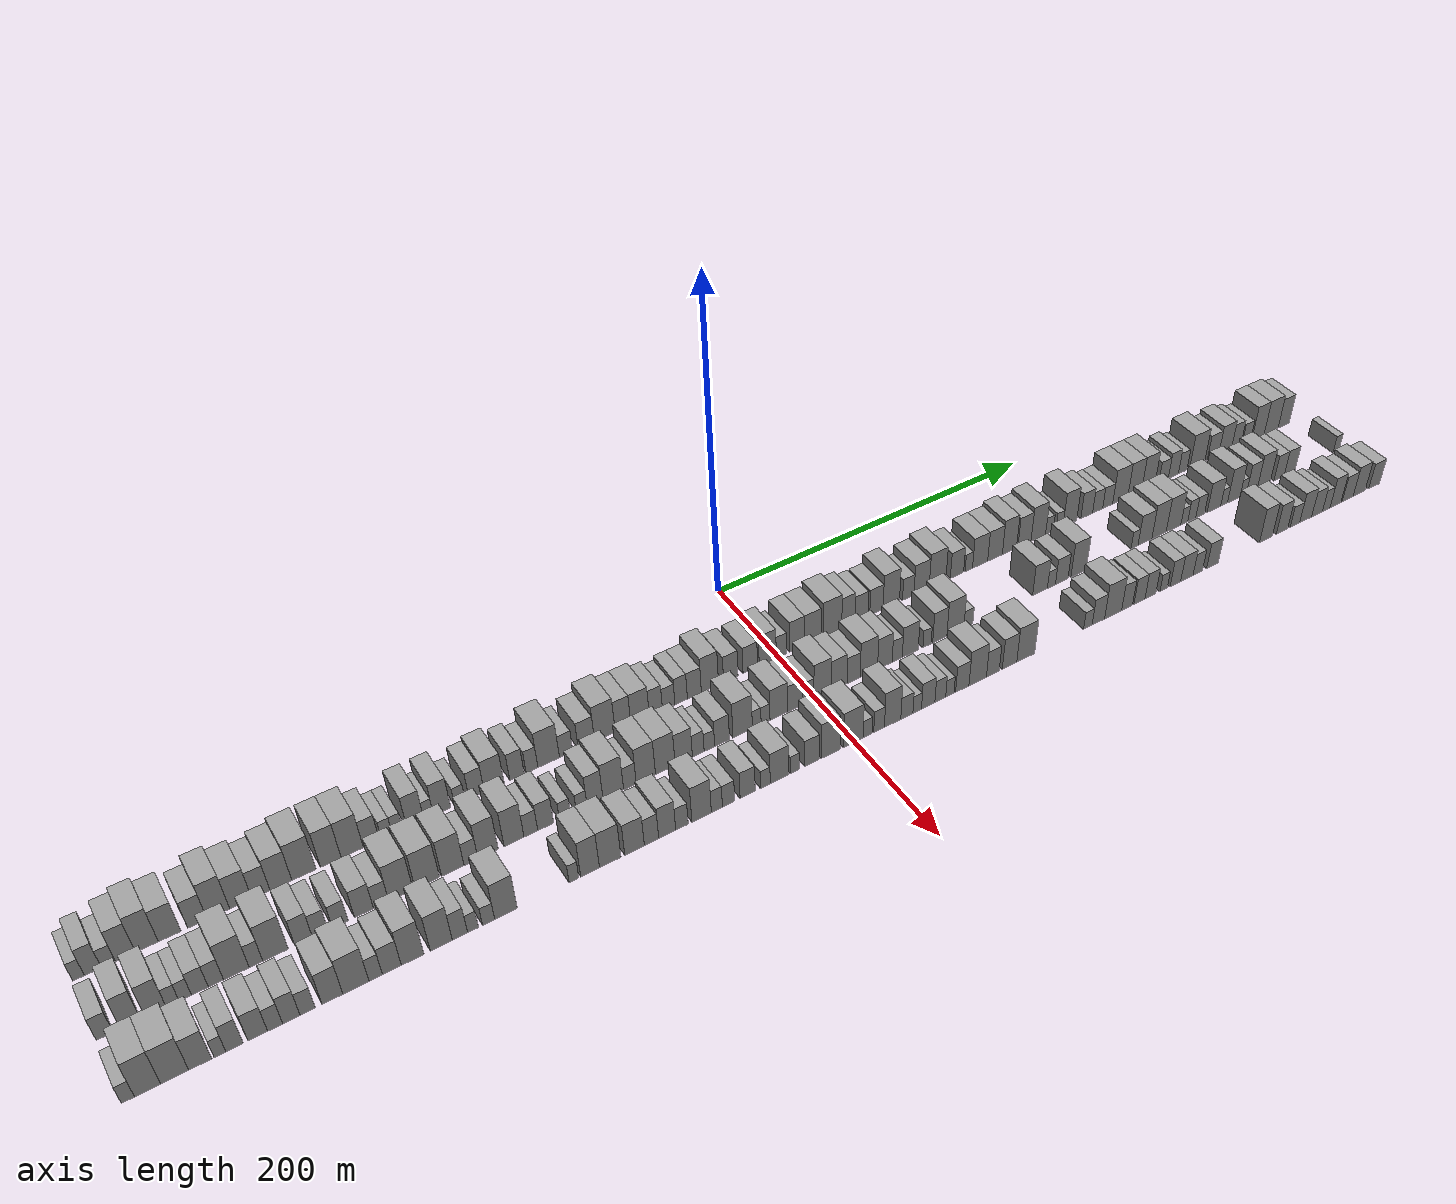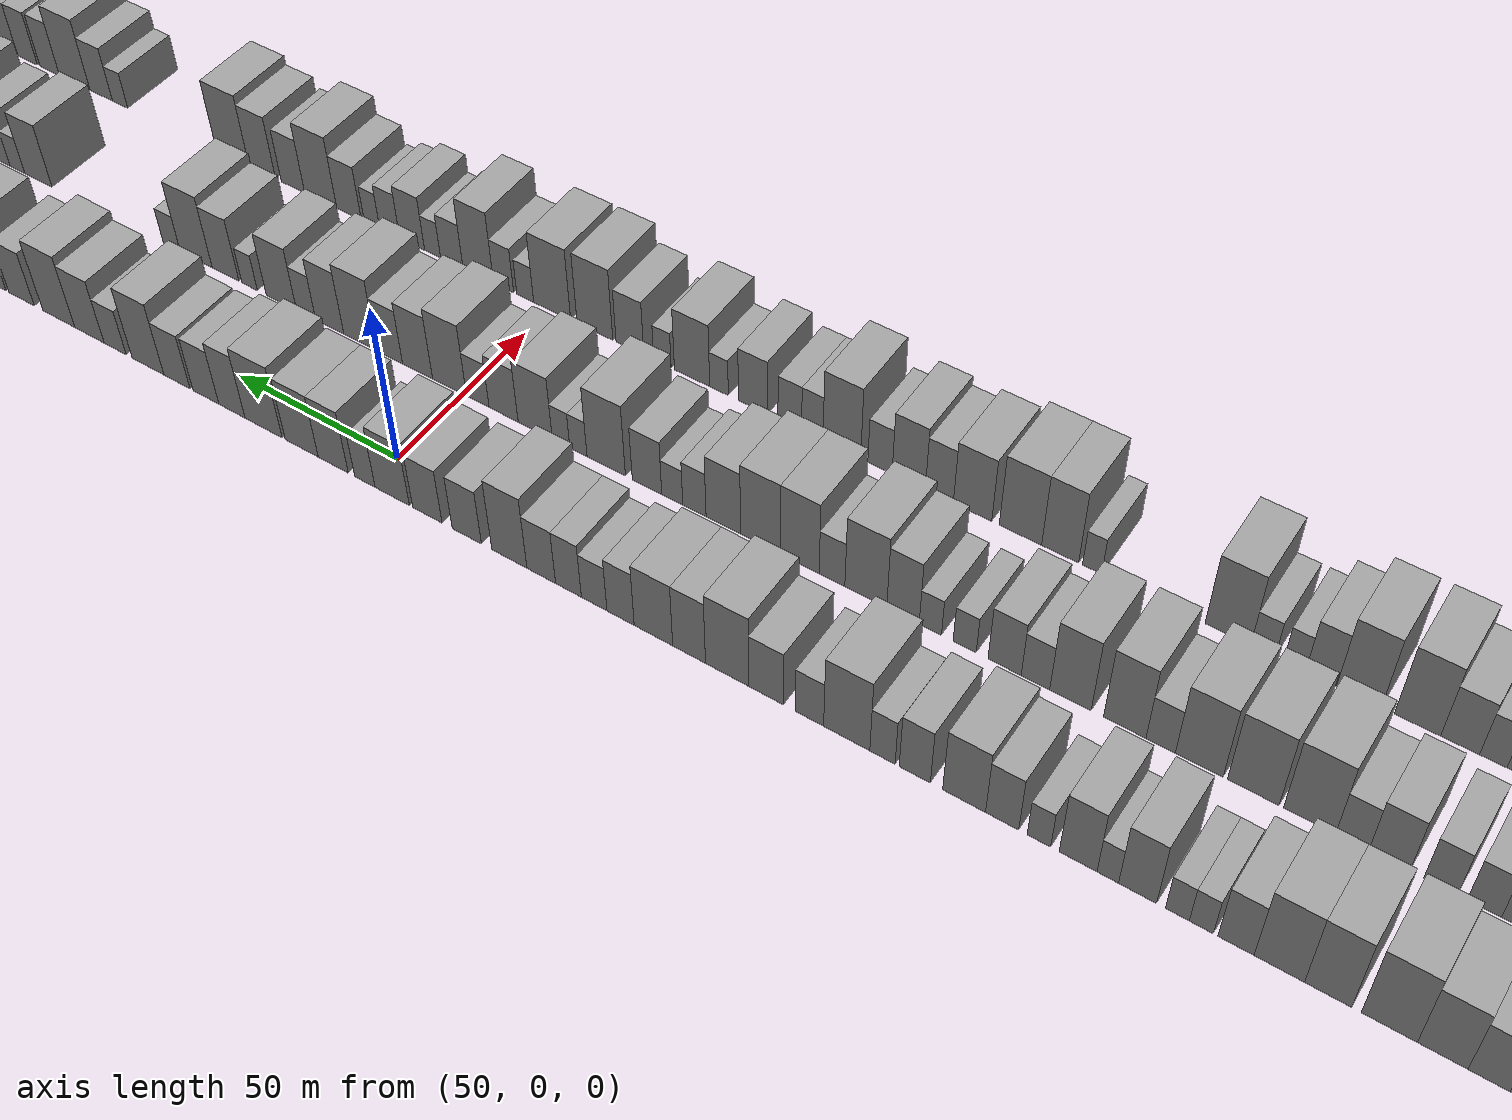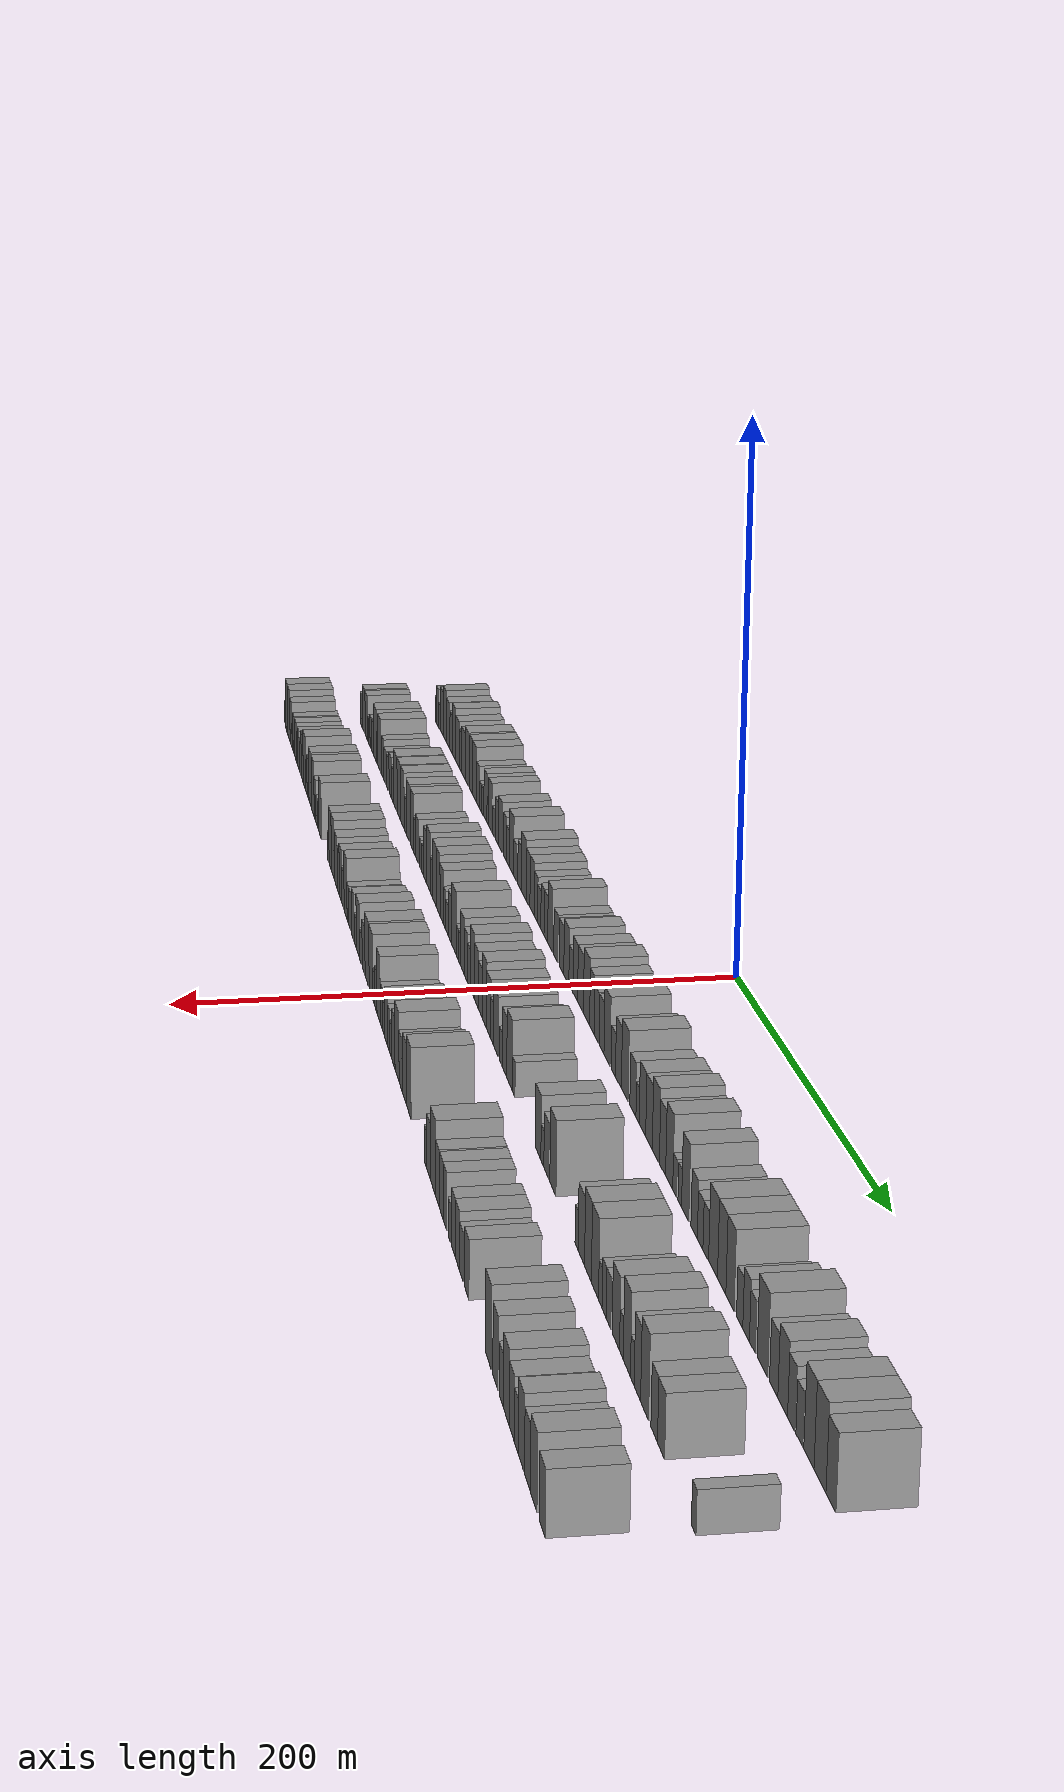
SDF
<sdf version="1.6">
 <world name="default">
  <scene>
   <sky><clouds><speed>12</speed></clouds></sky>
   <ambient>0.4 0.4 0.4 1</ambient>
   <background>0.7 0.7 0.7 1</background>
   <shadows>1</shadows>
  </scene>
  <gravity>0 0 -9.8066</gravity>
  <magnetic_field>6e-06 2.3e-05 -4.2e-05</magnetic_field>
  <physics default="0" name="default_physics" type="ode">
   <ode>
    <solver>
     <type>quick</type>
     <iters>10</iters>
     <sor>1.0</sor>
     <use_dynamic_moi_rescaling>0</use_dynamic_moi_rescaling>
    </solver>
    <constraints>
     <cfm>0</cfm>
     <erp>0.2</erp>
     <contact_max_correcting_vel>100</contact_max_correcting_vel>
     <contact_surface_layer>0.001</contact_surface_layer>
    </constraints>
   </ode>
   <max_step_size>0.004</max_step_size>
   <real_time_factor>1</real_time_factor>
   <real_time_update_rate>250</real_time_update_rate>
  </physics>
  <light name="sun" type="directional">
   <pose>0 0 10 0 0 0</pose>
   <diffuse>0.8 0.8 0.8 1</diffuse>
   <specular>0.2 0.2 0.2 1</specular>
   <attenuation>
    <range>1000</range>
    <constant>0.9</constant>
    <linear>0.01</linear>
    <quadratic>0.001</quadratic>
   </attenuation>
   <direction>-0.5 0.1 -0.9</direction>
  </light>
  <model name="building_1">
   <static>1</static>
   <pose>50.0000 -357.4880 0 0.000000 0.000000 0.000000</pose>
   <link name="link">
    <pose>0 0 6.00 0 0 0</pose>
    <collision name="collision"><geometry><box><size>20.0000 5.0240 12.0000</size></box></geometry></collision>
    <visual name="visual">
     <cast_shadows>0</cast_shadows>
     <geometry><box><size>20.0000 5.0240 12.0000</size></box></geometry>
     <material>
      <script>
       <uri>model://grey_wall/materials/scripts</uri>
       <uri>model://grey_wall/materials/textures</uri>
       <name>vrc/grey_wall</name>
      </script>
     </material>
    </visual>
   </link>
  </model>
  <model name="building_2">
   <static>1</static>
   <pose>50.0000 -351.3246 0 0.000000 0.000000 0.000000</pose>
   <link name="link">
    <pose>0 0 9.00 0 0 0</pose>
    <collision name="collision"><geometry><box><size>20.0000 7.3028 18.0000</size></box></geometry></collision>
    <visual name="visual">
     <cast_shadows>0</cast_shadows>
     <geometry><box><size>20.0000 7.3028 18.0000</size></box></geometry>
     <material>
      <script>
       <uri>model://grey_wall/materials/scripts</uri>
       <uri>model://grey_wall/materials/textures</uri>
       <name>vrc/grey_wall</name>
      </script>
     </material>
    </visual>
   </link>
  </model>
  <model name="building_3">
   <static>1</static>
   <pose>50.0000 -344.6761 0 0.000000 0.000000 0.000000</pose>
   <link name="link">
    <pose>0 0 6.00 0 0 0</pose>
    <collision name="collision"><geometry><box><size>20.0000 5.9943 12.0000</size></box></geometry></collision>
    <visual name="visual">
     <cast_shadows>0</cast_shadows>
     <geometry><box><size>20.0000 5.9943 12.0000</size></box></geometry>
     <material>
      <script>
       <uri>model://grey_wall/materials/scripts</uri>
       <uri>model://grey_wall/materials/textures</uri>
       <name>vrc/grey_wall</name>
      </script>
     </material>
    </visual>
   </link>
  </model>
  <model name="building_4">
   <static>1</static>
   <pose>50.0000 -337.2562 0 0.000000 0.000000 0.000000</pose>
   <link name="link">
    <pose>0 0 10.50 0 0 0</pose>
    <collision name="collision"><geometry><box><size>20.0000 8.8454 21.0000</size></box></geometry></collision>
    <visual name="visual">
     <cast_shadows>0</cast_shadows>
     <geometry><box><size>20.0000 8.8454 21.0000</size></box></geometry>
     <material>
      <script>
       <uri>model://grey_wall/materials/scripts</uri>
       <uri>model://grey_wall/materials/textures</uri>
       <name>vrc/grey_wall</name>
      </script>
     </material>
    </visual>
   </link>
  </model>
  <model name="building_5">
   <static>1</static>
   <pose>50.0000 -327.7756 0 0.000000 0.000000 0.000000</pose>
   <link name="link">
    <pose>0 0 12.00 0 0 0</pose>
    <collision name="collision"><geometry><box><size>20.0000 10.1157 24.0000</size></box></geometry></collision>
    <visual name="visual">
     <cast_shadows>0</cast_shadows>
     <geometry><box><size>20.0000 10.1157 24.0000</size></box></geometry>
     <material>
      <script>
       <uri>model://grey_wall/materials/scripts</uri>
       <uri>model://grey_wall/materials/textures</uri>
       <name>vrc/grey_wall</name>
      </script>
     </material>
    </visual>
   </link>
  </model>
  <model name="building_6">
   <static>1</static>
   <pose>50.0000 -317.6437 0 0.000000 0.000000 0.000000</pose>
   <link name="link">
    <pose>0 0 10.50 0 0 0</pose>
    <collision name="collision"><geometry><box><size>20.0000 10.1482 21.0000</size></box></geometry></collision>
    <visual name="visual">
     <cast_shadows>0</cast_shadows>
     <geometry><box><size>20.0000 10.1482 21.0000</size></box></geometry>
     <material>
      <script>
       <uri>model://grey_wall/materials/scripts</uri>
       <uri>model://grey_wall/materials/textures</uri>
       <name>vrc/grey_wall</name>
      </script>
     </material>
    </visual>
   </link>
  </model>
  <model name="building_7">
   <static>1</static>
   <pose>50.0000 -305.1972 0 0.000000 0.000000 0.000000</pose>
   <link name="link">
    <pose>0 0 9.00 0 0 0</pose>
    <collision name="collision"><geometry><box><size>20.0000 8.7449 18.0000</size></box></geometry></collision>
    <visual name="visual">
     <cast_shadows>0</cast_shadows>
     <geometry><box><size>20.0000 8.7449 18.0000</size></box></geometry>
     <material>
      <script>
       <uri>model://grey_wall/materials/scripts</uri>
       <uri>model://grey_wall/materials/textures</uri>
       <name>vrc/grey_wall</name>
      </script>
     </material>
    </visual>
   </link>
  </model>
  <model name="building_8">
   <static>1</static>
   <pose>50.0000 -295.6547 0 0.000000 0.000000 0.000000</pose>
   <link name="link">
    <pose>0 0 12.00 0 0 0</pose>
    <collision name="collision"><geometry><box><size>20.0000 10.3399 24.0000</size></box></geometry></collision>
    <visual name="visual">
     <cast_shadows>0</cast_shadows>
     <geometry><box><size>20.0000 10.3399 24.0000</size></box></geometry>
     <material>
      <script>
       <uri>model://grey_wall/materials/scripts</uri>
       <uri>model://grey_wall/materials/textures</uri>
       <name>vrc/grey_wall</name>
      </script>
     </material>
    </visual>
   </link>
  </model>
  <model name="building_9">
   <static>1</static>
   <pose>50.0000 -285.3415 0 0.000000 0.000000 0.000000</pose>
   <link name="link">
    <pose>0 0 10.50 0 0 0</pose>
    <collision name="collision"><geometry><box><size>20.0000 10.2866 21.0000</size></box></geometry></collision>
    <visual name="visual">
     <cast_shadows>0</cast_shadows>
     <geometry><box><size>20.0000 10.2866 21.0000</size></box></geometry>
     <material>
      <script>
       <uri>model://grey_wall/materials/scripts</uri>
       <uri>model://grey_wall/materials/textures</uri>
       <name>vrc/grey_wall</name>
      </script>
     </material>
    </visual>
   </link>
  </model>
  <model name="building_10">
   <static>1</static>
   <pose>50.0000 -275.9957 0 0.000000 0.000000 0.000000</pose>
   <link name="link">
    <pose>0 0 9.00 0 0 0</pose>
    <collision name="collision"><geometry><box><size>20.0000 8.4051 18.0000</size></box></geometry></collision>
    <visual name="visual">
     <cast_shadows>0</cast_shadows>
     <geometry><box><size>20.0000 8.4051 18.0000</size></box></geometry>
     <material>
      <script>
       <uri>model://grey_wall/materials/scripts</uri>
       <uri>model://grey_wall/materials/textures</uri>
       <name>vrc/grey_wall</name>
      </script>
     </material>
    </visual>
   </link>
  </model>
  <model name="building_11">
   <static>1</static>
   <pose>50.0000 -266.6467 0 0.000000 0.000000 0.000000</pose>
   <link name="link">
    <pose>0 0 10.50 0 0 0</pose>
    <collision name="collision"><geometry><box><size>20.0000 10.2929 21.0000</size></box></geometry></collision>
    <visual name="visual">
     <cast_shadows>0</cast_shadows>
     <geometry><box><size>20.0000 10.2929 21.0000</size></box></geometry>
     <material>
      <script>
       <uri>model://grey_wall/materials/scripts</uri>
       <uri>model://grey_wall/materials/textures</uri>
       <name>vrc/grey_wall</name>
      </script>
     </material>
    </visual>
   </link>
  </model>
  <model name="building_12">
   <static>1</static>
   <pose>50.0000 -255.6868 0 0.000000 0.000000 0.000000</pose>
   <link name="link">
    <pose>0 0 12.00 0 0 0</pose>
    <collision name="collision"><geometry><box><size>20.0000 11.6270 24.0000</size></box></geometry></collision>
    <visual name="visual">
     <cast_shadows>0</cast_shadows>
     <geometry><box><size>20.0000 11.6270 24.0000</size></box></geometry>
     <material>
      <script>
       <uri>model://grey_wall/materials/scripts</uri>
       <uri>model://grey_wall/materials/textures</uri>
       <name>vrc/grey_wall</name>
      </script>
     </material>
    </visual>
   </link>
  </model>
  <model name="building_13">
   <static>1</static>
   <pose>50.0000 -242.8772 0 0.000000 0.000000 0.000000</pose>
   <link name="link">
    <pose>0 0 12.00 0 0 0</pose>
    <collision name="collision"><geometry><box><size>20.0000 9.9921 24.0000</size></box></geometry></collision>
    <visual name="visual">
     <cast_shadows>0</cast_shadows>
     <geometry><box><size>20.0000 9.9921 24.0000</size></box></geometry>
     <material>
      <script>
       <uri>model://grey_wall/materials/scripts</uri>
       <uri>model://grey_wall/materials/textures</uri>
       <name>vrc/grey_wall</name>
      </script>
     </material>
    </visual>
   </link>
  </model>
  <model name="building_14">
   <static>1</static>
   <pose>50.0000 -232.4573 0 0.000000 0.000000 0.000000</pose>
   <link name="link">
    <pose>0 0 12.00 0 0 0</pose>
    <collision name="collision"><geometry><box><size>20.0000 10.8477 24.0000</size></box></geometry></collision>
    <visual name="visual">
     <cast_shadows>0</cast_shadows>
     <geometry><box><size>20.0000 10.8477 24.0000</size></box></geometry>
     <material>
      <script>
       <uri>model://grey_wall/materials/scripts</uri>
       <uri>model://grey_wall/materials/textures</uri>
       <name>vrc/grey_wall</name>
      </script>
     </material>
    </visual>
   </link>
  </model>
  <model name="building_15">
   <static>1</static>
   <pose>50.0000 -223.0720 0 0.000000 0.000000 0.000000</pose>
   <link name="link">
    <pose>0 0 9.00 0 0 0</pose>
    <collision name="collision"><geometry><box><size>20.0000 7.9230 18.0000</size></box></geometry></collision>
    <visual name="visual">
     <cast_shadows>0</cast_shadows>
     <geometry><box><size>20.0000 7.9230 18.0000</size></box></geometry>
     <material>
      <script>
       <uri>model://grey_wall/materials/scripts</uri>
       <uri>model://grey_wall/materials/textures</uri>
       <name>vrc/grey_wall</name>
      </script>
     </material>
    </visual>
   </link>
  </model>
  <model name="building_16">
   <static>1</static>
   <pose>50.0000 -215.4568 0 0.000000 0.000000 0.000000</pose>
   <link name="link">
    <pose>0 0 6.00 0 0 0</pose>
    <collision name="collision"><geometry><box><size>20.0000 5.3074 12.0000</size></box></geometry></collision>
    <visual name="visual">
     <cast_shadows>0</cast_shadows>
     <geometry><box><size>20.0000 5.3074 12.0000</size></box></geometry>
     <material>
      <script>
       <uri>model://grey_wall/materials/scripts</uri>
       <uri>model://grey_wall/materials/textures</uri>
       <name>vrc/grey_wall</name>
      </script>
     </material>
    </visual>
   </link>
  </model>
  <model name="building_17">
   <static>1</static>
   <pose>50.0000 -210.1444 0 0.000000 0.000000 0.000000</pose>
   <link name="link">
    <pose>0 0 6.00 0 0 0</pose>
    <collision name="collision"><geometry><box><size>20.0000 5.3173 12.0000</size></box></geometry></collision>
    <visual name="visual">
     <cast_shadows>0</cast_shadows>
     <geometry><box><size>20.0000 5.3173 12.0000</size></box></geometry>
     <material>
      <script>
       <uri>model://grey_wall/materials/scripts</uri>
       <uri>model://grey_wall/materials/textures</uri>
       <name>vrc/grey_wall</name>
      </script>
     </material>
    </visual>
   </link>
  </model>
  <model name="building_18">
   <static>1</static>
   <pose>50.0000 -201.1843 0 0.000000 0.000000 0.000000</pose>
   <link name="link">
    <pose>0 0 10.50 0 0 0</pose>
    <collision name="collision"><geometry><box><size>20.0000 8.6029 21.0000</size></box></geometry></collision>
    <visual name="visual">
     <cast_shadows>0</cast_shadows>
     <geometry><box><size>20.0000 8.6029 21.0000</size></box></geometry>
     <material>
      <script>
       <uri>model://grey_wall/materials/scripts</uri>
       <uri>model://grey_wall/materials/textures</uri>
       <name>vrc/grey_wall</name>
      </script>
     </material>
    </visual>
   </link>
  </model>
  <model name="building_19">
   <static>1</static>
   <pose>50.0000 -194.4160 0 0.000000 0.000000 0.000000</pose>
   <link name="link">
    <pose>0 0 6.00 0 0 0</pose>
    <collision name="collision"><geometry><box><size>20.0000 4.9338 12.0000</size></box></geometry></collision>
    <visual name="visual">
     <cast_shadows>0</cast_shadows>
     <geometry><box><size>20.0000 4.9338 12.0000</size></box></geometry>
     <material>
      <script>
       <uri>model://grey_wall/materials/scripts</uri>
       <uri>model://grey_wall/materials/textures</uri>
       <name>vrc/grey_wall</name>
      </script>
     </material>
    </visual>
   </link>
  </model>
  <model name="building_20">
   <static>1</static>
   <pose>50.0000 -187.5790 0 0.000000 0.000000 0.000000</pose>
   <link name="link">
    <pose>0 0 10.50 0 0 0</pose>
    <collision name="collision"><geometry><box><size>20.0000 8.7402 21.0000</size></box></geometry></collision>
    <visual name="visual">
     <cast_shadows>0</cast_shadows>
     <geometry><box><size>20.0000 8.7402 21.0000</size></box></geometry>
     <material>
      <script>
       <uri>model://grey_wall/materials/scripts</uri>
       <uri>model://grey_wall/materials/textures</uri>
       <name>vrc/grey_wall</name>
      </script>
     </material>
    </visual>
   </link>
  </model>
  <model name="building_21">
   <static>1</static>
   <pose>50.0000 -178.4539 0 0.000000 0.000000 0.000000</pose>
   <link name="link">
    <pose>0 0 6.00 0 0 0</pose>
    <collision name="collision"><geometry><box><size>20.0000 5.5102 12.0000</size></box></geometry></collision>
    <visual name="visual">
     <cast_shadows>0</cast_shadows>
     <geometry><box><size>20.0000 5.5102 12.0000</size></box></geometry>
     <material>
      <script>
       <uri>model://grey_wall/materials/scripts</uri>
       <uri>model://grey_wall/materials/textures</uri>
       <name>vrc/grey_wall</name>
      </script>
     </material>
    </visual>
   </link>
  </model>
  <model name="building_22">
   <static>1</static>
   <pose>50.0000 -169.7559 0 0.000000 0.000000 0.000000</pose>
   <link name="link">
    <pose>0 0 9.00 0 0 0</pose>
    <collision name="collision"><geometry><box><size>20.0000 7.8857 18.0000</size></box></geometry></collision>
    <visual name="visual">
     <cast_shadows>0</cast_shadows>
     <geometry><box><size>20.0000 7.8857 18.0000</size></box></geometry>
     <material>
      <script>
       <uri>model://grey_wall/materials/scripts</uri>
       <uri>model://grey_wall/materials/textures</uri>
       <name>vrc/grey_wall</name>
      </script>
     </material>
    </visual>
   </link>
  </model>
  <model name="building_23">
   <static>1</static>
   <pose>50.0000 -160.6477 0 0.000000 0.000000 0.000000</pose>
   <link name="link">
    <pose>0 0 10.50 0 0 0</pose>
    <collision name="collision"><geometry><box><size>20.0000 10.3306 21.0000</size></box></geometry></collision>
    <visual name="visual">
     <cast_shadows>0</cast_shadows>
     <geometry><box><size>20.0000 10.3306 21.0000</size></box></geometry>
     <material>
      <script>
       <uri>model://grey_wall/materials/scripts</uri>
       <uri>model://grey_wall/materials/textures</uri>
       <name>vrc/grey_wall</name>
      </script>
     </material>
    </visual>
   </link>
  </model>
  <model name="building_24">
   <static>1</static>
   <pose>50.0000 -148.6512 0 0.000000 0.000000 0.000000</pose>
   <link name="link">
    <pose>0 0 9.00 0 0 0</pose>
    <collision name="collision"><geometry><box><size>20.0000 7.6624 18.0000</size></box></geometry></collision>
    <visual name="visual">
     <cast_shadows>0</cast_shadows>
     <geometry><box><size>20.0000 7.6624 18.0000</size></box></geometry>
     <material>
      <script>
       <uri>model://grey_wall/materials/scripts</uri>
       <uri>model://grey_wall/materials/textures</uri>
       <name>vrc/grey_wall</name>
      </script>
     </material>
    </visual>
   </link>
  </model>
  <model name="building_25">
   <static>1</static>
   <pose>50.0000 -140.6782 0 0.000000 0.000000 0.000000</pose>
   <link name="link">
    <pose>0 0 7.50 0 0 0</pose>
    <collision name="collision"><geometry><box><size>20.0000 6.2836 15.0000</size></box></geometry></collision>
    <visual name="visual">
     <cast_shadows>0</cast_shadows>
     <geometry><box><size>20.0000 6.2836 15.0000</size></box></geometry>
     <material>
      <script>
       <uri>model://grey_wall/materials/scripts</uri>
       <uri>model://grey_wall/materials/textures</uri>
       <name>vrc/grey_wall</name>
      </script>
     </material>
    </visual>
   </link>
  </model>
  <model name="building_26">
   <static>1</static>
   <pose>50.0000 -131.7145 0 0.000000 0.000000 0.000000</pose>
   <link name="link">
    <pose>0 0 12.00 0 0 0</pose>
    <collision name="collision"><geometry><box><size>20.0000 11.6438 24.0000</size></box></geometry></collision>
    <visual name="visual">
     <cast_shadows>0</cast_shadows>
     <geometry><box><size>20.0000 11.6438 24.0000</size></box></geometry>
     <material>
      <script>
       <uri>model://grey_wall/materials/scripts</uri>
       <uri>model://grey_wall/materials/textures</uri>
       <name>vrc/grey_wall</name>
      </script>
     </material>
    </visual>
   </link>
  </model>
  <model name="building_27">
   <static>1</static>
   <pose>50.0000 -122.2554 0 0.000000 0.000000 0.000000</pose>
   <link name="link">
    <pose>0 0 7.50 0 0 0</pose>
    <collision name="collision"><geometry><box><size>20.0000 7.2743 15.0000</size></box></geometry></collision>
    <visual name="visual">
     <cast_shadows>0</cast_shadows>
     <geometry><box><size>20.0000 7.2743 15.0000</size></box></geometry>
     <material>
      <script>
       <uri>model://grey_wall/materials/scripts</uri>
       <uri>model://grey_wall/materials/textures</uri>
       <name>vrc/grey_wall</name>
      </script>
     </material>
    </visual>
   </link>
  </model>
  <model name="building_28">
   <static>1</static>
   <pose>50.0000 -111.1314 0 0.000000 0.000000 0.000000</pose>
   <link name="link">
    <pose>0 0 9.00 0 0 0</pose>
    <collision name="collision"><geometry><box><size>20.0000 8.9738 18.0000</size></box></geometry></collision>
    <visual name="visual">
     <cast_shadows>0</cast_shadows>
     <geometry><box><size>20.0000 8.9738 18.0000</size></box></geometry>
     <material>
      <script>
       <uri>model://grey_wall/materials/scripts</uri>
       <uri>model://grey_wall/materials/textures</uri>
       <name>vrc/grey_wall</name>
      </script>
     </material>
    </visual>
   </link>
  </model>
  <model name="building_29">
   <static>1</static>
   <pose>50.0000 -100.9214 0 0.000000 0.000000 0.000000</pose>
   <link name="link">
    <pose>0 0 12.00 0 0 0</pose>
    <collision name="collision"><geometry><box><size>20.0000 11.4462 24.0000</size></box></geometry></collision>
    <visual name="visual">
     <cast_shadows>0</cast_shadows>
     <geometry><box><size>20.0000 11.4462 24.0000</size></box></geometry>
     <material>
      <script>
       <uri>model://grey_wall/materials/scripts</uri>
       <uri>model://grey_wall/materials/textures</uri>
       <name>vrc/grey_wall</name>
      </script>
     </material>
    </visual>
   </link>
  </model>
  <model name="building_30">
   <static>1</static>
   <pose>50.0000 -90.8054 0 0.000000 0.000000 0.000000</pose>
   <link name="link">
    <pose>0 0 10.50 0 0 0</pose>
    <collision name="collision"><geometry><box><size>20.0000 8.7860 21.0000</size></box></geometry></collision>
    <visual name="visual">
     <cast_shadows>0</cast_shadows>
     <geometry><box><size>20.0000 8.7860 21.0000</size></box></geometry>
     <material>
      <script>
       <uri>model://grey_wall/materials/scripts</uri>
       <uri>model://grey_wall/materials/textures</uri>
       <name>vrc/grey_wall</name>
      </script>
     </material>
    </visual>
   </link>
  </model>
  <model name="building_31">
   <static>1</static>
   <pose>50.0000 -81.1889 0 0.000000 0.000000 0.000000</pose>
   <link name="link">
    <pose>0 0 10.50 0 0 0</pose>
    <collision name="collision"><geometry><box><size>20.0000 10.4469 21.0000</size></box></geometry></collision>
    <visual name="visual">
     <cast_shadows>0</cast_shadows>
     <geometry><box><size>20.0000 10.4469 21.0000</size></box></geometry>
     <material>
      <script>
       <uri>model://grey_wall/materials/scripts</uri>
       <uri>model://grey_wall/materials/textures</uri>
       <name>vrc/grey_wall</name>
      </script>
     </material>
    </visual>
   </link>
  </model>
  <model name="building_32">
   <static>1</static>
   <pose>50.0000 -72.2218 0 0.000000 0.000000 0.000000</pose>
   <link name="link">
    <pose>0 0 9.00 0 0 0</pose>
    <collision name="collision"><geometry><box><size>20.0000 7.4873 18.0000</size></box></geometry></collision>
    <visual name="visual">
     <cast_shadows>0</cast_shadows>
     <geometry><box><size>20.0000 7.4873 18.0000</size></box></geometry>
     <material>
      <script>
       <uri>model://grey_wall/materials/scripts</uri>
       <uri>model://grey_wall/materials/textures</uri>
       <name>vrc/grey_wall</name>
      </script>
     </material>
    </visual>
   </link>
  </model>
  <model name="building_33">
   <static>1</static>
   <pose>50.0000 -64.9223 0 0.000000 0.000000 0.000000</pose>
   <link name="link">
    <pose>0 0 7.50 0 0 0</pose>
    <collision name="collision"><geometry><box><size>20.0000 7.1118 15.0000</size></box></geometry></collision>
    <visual name="visual">
     <cast_shadows>0</cast_shadows>
     <geometry><box><size>20.0000 7.1118 15.0000</size></box></geometry>
     <material>
      <script>
       <uri>model://grey_wall/materials/scripts</uri>
       <uri>model://grey_wall/materials/textures</uri>
       <name>vrc/grey_wall</name>
      </script>
     </material>
    </visual>
   </link>
  </model>
  <model name="building_34">
   <static>1</static>
   <pose>50.0000 -57.7471 0 0.000000 0.000000 0.000000</pose>
   <link name="link">
    <pose>0 0 9.00 0 0 0</pose>
    <collision name="collision"><geometry><box><size>20.0000 7.2385 18.0000</size></box></geometry></collision>
    <visual name="visual">
     <cast_shadows>0</cast_shadows>
     <geometry><box><size>20.0000 7.2385 18.0000</size></box></geometry>
     <material>
      <script>
       <uri>model://grey_wall/materials/scripts</uri>
       <uri>model://grey_wall/materials/textures</uri>
       <name>vrc/grey_wall</name>
      </script>
     </material>
    </visual>
   </link>
  </model>
  <model name="building_35">
   <static>1</static>
   <pose>50.0000 -50.0649 0 0.000000 0.000000 0.000000</pose>
   <link name="link">
    <pose>0 0 9.00 0 0 0</pose>
    <collision name="collision"><geometry><box><size>20.0000 8.1259 18.0000</size></box></geometry></collision>
    <visual name="visual">
     <cast_shadows>0</cast_shadows>
     <geometry><box><size>20.0000 8.1259 18.0000</size></box></geometry>
     <material>
      <script>
       <uri>model://grey_wall/materials/scripts</uri>
       <uri>model://grey_wall/materials/textures</uri>
       <name>vrc/grey_wall</name>
      </script>
     </material>
    </visual>
   </link>
  </model>
  <model name="building_36">
   <static>1</static>
   <pose>50.0000 -40.9510 0 0.000000 0.000000 0.000000</pose>
   <link name="link">
    <pose>0 0 12.00 0 0 0</pose>
    <collision name="collision"><geometry><box><size>20.0000 10.1020 24.0000</size></box></geometry></collision>
    <visual name="visual">
     <cast_shadows>0</cast_shadows>
     <geometry><box><size>20.0000 10.1020 24.0000</size></box></geometry>
     <material>
      <script>
       <uri>model://grey_wall/materials/scripts</uri>
       <uri>model://grey_wall/materials/textures</uri>
       <name>vrc/grey_wall</name>
      </script>
     </material>
    </visual>
   </link>
  </model>
  <model name="building_37">
   <static>1</static>
   <pose>50.0000 -28.6230 0 0.000000 0.000000 0.000000</pose>
   <link name="link">
    <pose>0 0 9.00 0 0 0</pose>
    <collision name="collision"><geometry><box><size>20.0000 8.5541 18.0000</size></box></geometry></collision>
    <visual name="visual">
     <cast_shadows>0</cast_shadows>
     <geometry><box><size>20.0000 8.5541 18.0000</size></box></geometry>
     <material>
      <script>
       <uri>model://grey_wall/materials/scripts</uri>
       <uri>model://grey_wall/materials/textures</uri>
       <name>vrc/grey_wall</name>
      </script>
     </material>
    </visual>
   </link>
  </model>
  <model name="building_38">
   <static>1</static>
   <pose>50.0000 -16.9877 0 0.000000 0.000000 0.000000</pose>
   <link name="link">
    <pose>0 0 9.00 0 0 0</pose>
    <collision name="collision"><geometry><box><size>20.0000 8.7164 18.0000</size></box></geometry></collision>
    <visual name="visual">
     <cast_shadows>0</cast_shadows>
     <geometry><box><size>20.0000 8.7164 18.0000</size></box></geometry>
     <material>
      <script>
       <uri>model://grey_wall/materials/scripts</uri>
       <uri>model://grey_wall/materials/textures</uri>
       <name>vrc/grey_wall</name>
      </script>
     </material>
    </visual>
   </link>
  </model>
  <model name="building_39">
   <static>1</static>
   <pose>50.0000 -6.4514 0 0.000000 0.000000 0.000000</pose>
   <link name="link">
    <pose>0 0 10.50 0 0 0</pose>
    <collision name="collision"><geometry><box><size>20.0000 10.3563 21.0000</size></box></geometry></collision>
    <visual name="visual">
     <cast_shadows>0</cast_shadows>
     <geometry><box><size>20.0000 10.3563 21.0000</size></box></geometry>
     <material>
      <script>
       <uri>model://grey_wall/materials/scripts</uri>
       <uri>model://grey_wall/materials/textures</uri>
       <name>vrc/grey_wall</name>
      </script>
     </material>
    </visual>
   </link>
  </model>
  <model name="building_40">
   <static>1</static>
   <pose>50.0000 1.8156 0 0.000000 0.000000 0.000000</pose>
   <link name="link">
    <pose>0 0 7.50 0 0 0</pose>
    <collision name="collision"><geometry><box><size>20.0000 6.1777 15.0000</size></box></geometry></collision>
    <visual name="visual">
     <cast_shadows>0</cast_shadows>
     <geometry><box><size>20.0000 6.1777 15.0000</size></box></geometry>
     <material>
      <script>
       <uri>model://grey_wall/materials/scripts</uri>
       <uri>model://grey_wall/materials/textures</uri>
       <name>vrc/grey_wall</name>
      </script>
     </material>
    </visual>
   </link>
  </model>
  <model name="building_41">
   <static>1</static>
   <pose>50.0000 11.5562 0 0.000000 0.000000 0.000000</pose>
   <link name="link">
    <pose>0 0 10.50 0 0 0</pose>
    <collision name="collision"><geometry><box><size>20.0000 9.3035 21.0000</size></box></geometry></collision>
    <visual name="visual">
     <cast_shadows>0</cast_shadows>
     <geometry><box><size>20.0000 9.3035 21.0000</size></box></geometry>
     <material>
      <script>
       <uri>model://grey_wall/materials/scripts</uri>
       <uri>model://grey_wall/materials/textures</uri>
       <name>vrc/grey_wall</name>
      </script>
     </material>
    </visual>
   </link>
  </model>
  <model name="building_42">
   <static>1</static>
   <pose>50.0000 21.3764 0 0.000000 0.000000 0.000000</pose>
   <link name="link">
    <pose>0 0 10.50 0 0 0</pose>
    <collision name="collision"><geometry><box><size>20.0000 10.3369 21.0000</size></box></geometry></collision>
    <visual name="visual">
     <cast_shadows>0</cast_shadows>
     <geometry><box><size>20.0000 10.3369 21.0000</size></box></geometry>
     <material>
      <script>
       <uri>model://grey_wall/materials/scripts</uri>
       <uri>model://grey_wall/materials/textures</uri>
       <name>vrc/grey_wall</name>
      </script>
     </material>
    </visual>
   </link>
  </model>
  <model name="building_43">
   <static>1</static>
   <pose>50.0000 33.4431 0 0.000000 0.000000 0.000000</pose>
   <link name="link">
    <pose>0 0 12.00 0 0 0</pose>
    <collision name="collision"><geometry><box><size>20.0000 11.7965 24.0000</size></box></geometry></collision>
    <visual name="visual">
     <cast_shadows>0</cast_shadows>
     <geometry><box><size>20.0000 11.7965 24.0000</size></box></geometry>
     <material>
      <script>
       <uri>model://grey_wall/materials/scripts</uri>
       <uri>model://grey_wall/materials/textures</uri>
       <name>vrc/grey_wall</name>
      </script>
     </material>
    </visual>
   </link>
  </model>
  <model name="building_44">
   <static>1</static>
   <pose>50.0000 43.5559 0 0.000000 0.000000 0.000000</pose>
   <link name="link">
    <pose>0 0 10.50 0 0 0</pose>
    <collision name="collision"><geometry><box><size>20.0000 8.4291 21.0000</size></box></geometry></collision>
    <visual name="visual">
     <cast_shadows>0</cast_shadows>
     <geometry><box><size>20.0000 8.4291 21.0000</size></box></geometry>
     <material>
      <script>
       <uri>model://grey_wall/materials/scripts</uri>
       <uri>model://grey_wall/materials/textures</uri>
       <name>vrc/grey_wall</name>
      </script>
     </material>
    </visual>
   </link>
  </model>
  <model name="building_45">
   <static>1</static>
   <pose>50.0000 51.9869 0 0.000000 0.000000 0.000000</pose>
   <link name="link">
    <pose>0 0 9.00 0 0 0</pose>
    <collision name="collision"><geometry><box><size>20.0000 8.4329 18.0000</size></box></geometry></collision>
    <visual name="visual">
     <cast_shadows>0</cast_shadows>
     <geometry><box><size>20.0000 8.4329 18.0000</size></box></geometry>
     <material>
      <script>
       <uri>model://grey_wall/materials/scripts</uri>
       <uri>model://grey_wall/materials/textures</uri>
       <name>vrc/grey_wall</name>
      </script>
     </material>
    </visual>
   </link>
  </model>
  <model name="building_46">
   <static>1</static>
   <pose>50.0000 61.5077 0 0.000000 0.000000 0.000000</pose>
   <link name="link">
    <pose>0 0 9.00 0 0 0</pose>
    <collision name="collision"><geometry><box><size>20.0000 8.6087 18.0000</size></box></geometry></collision>
    <visual name="visual">
     <cast_shadows>0</cast_shadows>
     <geometry><box><size>20.0000 8.6087 18.0000</size></box></geometry>
     <material>
      <script>
       <uri>model://grey_wall/materials/scripts</uri>
       <uri>model://grey_wall/materials/textures</uri>
       <name>vrc/grey_wall</name>
      </script>
     </material>
    </visual>
   </link>
  </model>
  <model name="building_47">
   <static>1</static>
   <pose>50.0000 71.1475 0 0.000000 0.000000 0.000000</pose>
   <link name="link">
    <pose>0 0 12.00 0 0 0</pose>
    <collision name="collision"><geometry><box><size>20.0000 10.6708 24.0000</size></box></geometry></collision>
    <visual name="visual">
     <cast_shadows>0</cast_shadows>
     <geometry><box><size>20.0000 10.6708 24.0000</size></box></geometry>
     <material>
      <script>
       <uri>model://grey_wall/materials/scripts</uri>
       <uri>model://grey_wall/materials/textures</uri>
       <name>vrc/grey_wall</name>
      </script>
     </material>
    </visual>
   </link>
  </model>
  <model name="building_48">
   <static>1</static>
   <pose>50.0000 82.2222 0 0.000000 0.000000 0.000000</pose>
   <link name="link">
    <pose>0 0 7.50 0 0 0</pose>
    <collision name="collision"><geometry><box><size>20.0000 7.4786 15.0000</size></box></geometry></collision>
    <visual name="visual">
     <cast_shadows>0</cast_shadows>
     <geometry><box><size>20.0000 7.4786 15.0000</size></box></geometry>
     <material>
      <script>
       <uri>model://grey_wall/materials/scripts</uri>
       <uri>model://grey_wall/materials/textures</uri>
       <name>vrc/grey_wall</name>
      </script>
     </material>
    </visual>
   </link>
  </model>
  <model name="building_49">
   <static>1</static>
   <pose>50.0000 91.0026 0 0.000000 0.000000 0.000000</pose>
   <link name="link">
    <pose>0 0 10.50 0 0 0</pose>
    <collision name="collision"><geometry><box><size>20.0000 10.0822 21.0000</size></box></geometry></collision>
    <visual name="visual">
     <cast_shadows>0</cast_shadows>
     <geometry><box><size>20.0000 10.0822 21.0000</size></box></geometry>
     <material>
      <script>
       <uri>model://grey_wall/materials/scripts</uri>
       <uri>model://grey_wall/materials/textures</uri>
       <name>vrc/grey_wall</name>
      </script>
     </material>
    </visual>
   </link>
  </model>
  <model name="building_50">
   <static>1</static>
   <pose>50.0000 101.6119 0 0.000000 0.000000 0.000000</pose>
   <link name="link">
    <pose>0 0 12.00 0 0 0</pose>
    <collision name="collision"><geometry><box><size>20.0000 11.1366 24.0000</size></box></geometry></collision>
    <visual name="visual">
     <cast_shadows>0</cast_shadows>
     <geometry><box><size>20.0000 11.1366 24.0000</size></box></geometry>
     <material>
      <script>
       <uri>model://grey_wall/materials/scripts</uri>
       <uri>model://grey_wall/materials/textures</uri>
       <name>vrc/grey_wall</name>
      </script>
     </material>
    </visual>
   </link>
  </model>
  <model name="building_51">
   <static>1</static>
   <pose>50.0000 114.6626 0 0.000000 0.000000 0.000000</pose>
   <link name="link">
    <pose>0 0 9.00 0 0 0</pose>
    <collision name="collision"><geometry><box><size>20.0000 8.9647 18.0000</size></box></geometry></collision>
    <visual name="visual">
     <cast_shadows>0</cast_shadows>
     <geometry><box><size>20.0000 8.9647 18.0000</size></box></geometry>
     <material>
      <script>
       <uri>model://grey_wall/materials/scripts</uri>
       <uri>model://grey_wall/materials/textures</uri>
       <name>vrc/grey_wall</name>
      </script>
     </material>
    </visual>
   </link>
  </model>
  <model name="building_52">
   <static>1</static>
   <pose>50.0000 122.6843 0 0.000000 0.000000 0.000000</pose>
   <link name="link">
    <pose>0 0 6.00 0 0 0</pose>
    <collision name="collision"><geometry><box><size>20.0000 5.0787 12.0000</size></box></geometry></collision>
    <visual name="visual">
     <cast_shadows>0</cast_shadows>
     <geometry><box><size>20.0000 5.0787 12.0000</size></box></geometry>
     <material>
      <script>
       <uri>model://grey_wall/materials/scripts</uri>
       <uri>model://grey_wall/materials/textures</uri>
       <name>vrc/grey_wall</name>
      </script>
     </material>
    </visual>
   </link>
  </model>
  <model name="building_53">
   <static>1</static>
   <pose>50.0000 130.4150 0 0.000000 0.000000 0.000000</pose>
   <link name="link">
    <pose>0 0 10.50 0 0 0</pose>
    <collision name="collision"><geometry><box><size>20.0000 10.3826 21.0000</size></box></geometry></collision>
    <visual name="visual">
     <cast_shadows>0</cast_shadows>
     <geometry><box><size>20.0000 10.3826 21.0000</size></box></geometry>
     <material>
      <script>
       <uri>model://grey_wall/materials/scripts</uri>
       <uri>model://grey_wall/materials/textures</uri>
       <name>vrc/grey_wall</name>
      </script>
     </material>
    </visual>
   </link>
  </model>
  <model name="building_54">
   <static>1</static>
   <pose>50.0000 140.6762 0 0.000000 0.000000 0.000000</pose>
   <link name="link">
    <pose>0 0 10.50 0 0 0</pose>
    <collision name="collision"><geometry><box><size>20.0000 10.1399 21.0000</size></box></geometry></collision>
    <visual name="visual">
     <cast_shadows>0</cast_shadows>
     <geometry><box><size>20.0000 10.1399 21.0000</size></box></geometry>
     <material>
      <script>
       <uri>model://grey_wall/materials/scripts</uri>
       <uri>model://grey_wall/materials/textures</uri>
       <name>vrc/grey_wall</name>
      </script>
     </material>
    </visual>
   </link>
  </model>
  <model name="building_55">
   <static>1</static>
   <pose>50.0000 150.6441 0 0.000000 0.000000 0.000000</pose>
   <link name="link">
    <pose>0 0 12.00 0 0 0</pose>
    <collision name="collision"><geometry><box><size>20.0000 9.7958 24.0000</size></box></geometry></collision>
    <visual name="visual">
     <cast_shadows>0</cast_shadows>
     <geometry><box><size>20.0000 9.7958 24.0000</size></box></geometry>
     <material>
      <script>
       <uri>model://grey_wall/materials/scripts</uri>
       <uri>model://grey_wall/materials/textures</uri>
       <name>vrc/grey_wall</name>
      </script>
     </material>
    </visual>
   </link>
  </model>
  <model name="building_56">
   <static>1</static>
   <pose>50.0000 161.1490 0 0.000000 0.000000 0.000000</pose>
   <link name="link">
    <pose>0 0 10.50 0 0 0</pose>
    <collision name="collision"><geometry><box><size>20.0000 9.2140 21.0000</size></box></geometry></collision>
    <visual name="visual">
     <cast_shadows>0</cast_shadows>
     <geometry><box><size>20.0000 9.2140 21.0000</size></box></geometry>
     <material>
      <script>
       <uri>model://grey_wall/materials/scripts</uri>
       <uri>model://grey_wall/materials/textures</uri>
       <name>vrc/grey_wall</name>
      </script>
     </material>
    </visual>
   </link>
  </model>
  <model name="building_57">
   <static>1</static>
   <pose>50.0000 170.9249 0 0.000000 0.000000 0.000000</pose>
   <link name="link">
    <pose>0 0 12.00 0 0 0</pose>
    <collision name="collision"><geometry><box><size>20.0000 10.3378 24.0000</size></box></geometry></collision>
    <visual name="visual">
     <cast_shadows>0</cast_shadows>
     <geometry><box><size>20.0000 10.3378 24.0000</size></box></geometry>
     <material>
      <script>
       <uri>model://grey_wall/materials/scripts</uri>
       <uri>model://grey_wall/materials/textures</uri>
       <name>vrc/grey_wall</name>
      </script>
     </material>
    </visual>
   </link>
  </model>
  <model name="building_58">
   <static>1</static>
   <pose>50.0000 178.8278 0 0.000000 0.000000 0.000000</pose>
   <link name="link">
    <pose>0 0 6.00 0 0 0</pose>
    <collision name="collision"><geometry><box><size>20.0000 5.4681 12.0000</size></box></geometry></collision>
    <visual name="visual">
     <cast_shadows>0</cast_shadows>
     <geometry><box><size>20.0000 5.4681 12.0000</size></box></geometry>
     <material>
      <script>
       <uri>model://grey_wall/materials/scripts</uri>
       <uri>model://grey_wall/materials/textures</uri>
       <name>vrc/grey_wall</name>
      </script>
     </material>
    </visual>
   </link>
  </model>
  <model name="building_59">
   <static>1</static>
   <pose>50.0000 186.0637 0 0.000000 0.000000 0.000000</pose>
   <link name="link">
    <pose>0 0 6.00 0 0 0</pose>
    <collision name="collision"><geometry><box><size>20.0000 5.0036 12.0000</size></box></geometry></collision>
    <visual name="visual">
     <cast_shadows>0</cast_shadows>
     <geometry><box><size>20.0000 5.0036 12.0000</size></box></geometry>
     <material>
      <script>
       <uri>model://grey_wall/materials/scripts</uri>
       <uri>model://grey_wall/materials/textures</uri>
       <name>vrc/grey_wall</name>
      </script>
     </material>
    </visual>
   </link>
  </model>
  <model name="building_60">
   <static>1</static>
   <pose>50.0000 193.5374 0 0.000000 0.000000 0.000000</pose>
   <link name="link">
    <pose>0 0 12.00 0 0 0</pose>
    <collision name="collision"><geometry><box><size>20.0000 9.9438 24.0000</size></box></geometry></collision>
    <visual name="visual">
     <cast_shadows>0</cast_shadows>
     <geometry><box><size>20.0000 9.9438 24.0000</size></box></geometry>
     <material>
      <script>
       <uri>model://grey_wall/materials/scripts</uri>
       <uri>model://grey_wall/materials/textures</uri>
       <name>vrc/grey_wall</name>
      </script>
     </material>
    </visual>
   </link>
  </model>
  <model name="building_61">
   <static>1</static>
   <pose>50.0000 205.8110 0 0.000000 0.000000 0.000000</pose>
   <link name="link">
    <pose>0 0 9.00 0 0 0</pose>
    <collision name="collision"><geometry><box><size>20.0000 8.6033 18.0000</size></box></geometry></collision>
    <visual name="visual">
     <cast_shadows>0</cast_shadows>
     <geometry><box><size>20.0000 8.6033 18.0000</size></box></geometry>
     <material>
      <script>
       <uri>model://grey_wall/materials/scripts</uri>
       <uri>model://grey_wall/materials/textures</uri>
       <name>vrc/grey_wall</name>
      </script>
     </material>
    </visual>
   </link>
  </model>
  <model name="building_62">
   <static>1</static>
   <pose>50.0000 213.8199 0 0.000000 0.000000 0.000000</pose>
   <link name="link">
    <pose>0 0 7.50 0 0 0</pose>
    <collision name="collision"><geometry><box><size>20.0000 7.4147 15.0000</size></box></geometry></collision>
    <visual name="visual">
     <cast_shadows>0</cast_shadows>
     <geometry><box><size>20.0000 7.4147 15.0000</size></box></geometry>
     <material>
      <script>
       <uri>model://grey_wall/materials/scripts</uri>
       <uri>model://grey_wall/materials/textures</uri>
       <name>vrc/grey_wall</name>
      </script>
     </material>
    </visual>
   </link>
  </model>
  <model name="building_63">
   <static>1</static>
   <pose>50.0000 221.2296 0 0.000000 0.000000 0.000000</pose>
   <link name="link">
    <pose>0 0 7.50 0 0 0</pose>
    <collision name="collision"><geometry><box><size>20.0000 7.4047 15.0000</size></box></geometry></collision>
    <visual name="visual">
     <cast_shadows>0</cast_shadows>
     <geometry><box><size>20.0000 7.4047 15.0000</size></box></geometry>
     <material>
      <script>
       <uri>model://grey_wall/materials/scripts</uri>
       <uri>model://grey_wall/materials/textures</uri>
       <name>vrc/grey_wall</name>
      </script>
     </material>
    </visual>
   </link>
  </model>
  <model name="building_64">
   <static>1</static>
   <pose>50.0000 230.5645 0 0.000000 0.000000 0.000000</pose>
   <link name="link">
    <pose>0 0 12.00 0 0 0</pose>
    <collision name="collision"><geometry><box><size>20.0000 11.2650 24.0000</size></box></geometry></collision>
    <visual name="visual">
     <cast_shadows>0</cast_shadows>
     <geometry><box><size>20.0000 11.2650 24.0000</size></box></geometry>
     <material>
      <script>
       <uri>model://grey_wall/materials/scripts</uri>
       <uri>model://grey_wall/materials/textures</uri>
       <name>vrc/grey_wall</name>
      </script>
     </material>
    </visual>
   </link>
  </model>
  <model name="building_65">
   <static>1</static>
   <pose>50.0000 241.3968 0 0.000000 0.000000 0.000000</pose>
   <link name="link">
    <pose>0 0 12.00 0 0 0</pose>
    <collision name="collision"><geometry><box><size>20.0000 10.3996 24.0000</size></box></geometry></collision>
    <visual name="visual">
     <cast_shadows>0</cast_shadows>
     <geometry><box><size>20.0000 10.3996 24.0000</size></box></geometry>
     <material>
      <script>
       <uri>model://grey_wall/materials/scripts</uri>
       <uri>model://grey_wall/materials/textures</uri>
       <name>vrc/grey_wall</name>
      </script>
     </material>
    </visual>
   </link>
  </model>
  <model name="building_66">
   <static>1</static>
   <pose>50.0000 251.5735 0 0.000000 0.000000 0.000000</pose>
   <link name="link">
    <pose>0 0 12.00 0 0 0</pose>
    <collision name="collision"><geometry><box><size>20.0000 9.9537 24.0000</size></box></geometry></collision>
    <visual name="visual">
     <cast_shadows>0</cast_shadows>
     <geometry><box><size>20.0000 9.9537 24.0000</size></box></geometry>
     <material>
      <script>
       <uri>model://grey_wall/materials/scripts</uri>
       <uri>model://grey_wall/materials/textures</uri>
       <name>vrc/grey_wall</name>
      </script>
     </material>
    </visual>
   </link>
  </model>
  <model name="building_67">
   <static>1</static>
   <pose>50.0000 263.2214 0 0.000000 0.000000 0.000000</pose>
   <link name="link">
    <pose>0 0 7.50 0 0 0</pose>
    <collision name="collision"><geometry><box><size>20.0000 7.3422 15.0000</size></box></geometry></collision>
    <visual name="visual">
     <cast_shadows>0</cast_shadows>
     <geometry><box><size>20.0000 7.3422 15.0000</size></box></geometry>
     <material>
      <script>
       <uri>model://grey_wall/materials/scripts</uri>
       <uri>model://grey_wall/materials/textures</uri>
       <name>vrc/grey_wall</name>
      </script>
     </material>
    </visual>
   </link>
  </model>
  <model name="building_68">
   <static>1</static>
   <pose>50.0000 270.7523 0 0.000000 0.000000 0.000000</pose>
   <link name="link">
    <pose>0 0 9.00 0 0 0</pose>
    <collision name="collision"><geometry><box><size>20.0000 7.7197 18.0000</size></box></geometry></collision>
    <visual name="visual">
     <cast_shadows>0</cast_shadows>
     <geometry><box><size>20.0000 7.7197 18.0000</size></box></geometry>
     <material>
      <script>
       <uri>model://grey_wall/materials/scripts</uri>
       <uri>model://grey_wall/materials/textures</uri>
       <name>vrc/grey_wall</name>
      </script>
     </material>
    </visual>
   </link>
  </model>
  <model name="building_69">
   <static>1</static>
   <pose>50.0000 277.9587 0 0.000000 0.000000 0.000000</pose>
   <link name="link">
    <pose>0 0 7.50 0 0 0</pose>
    <collision name="collision"><geometry><box><size>20.0000 6.6931 15.0000</size></box></geometry></collision>
    <visual name="visual">
     <cast_shadows>0</cast_shadows>
     <geometry><box><size>20.0000 6.6931 15.0000</size></box></geometry>
     <material>
      <script>
       <uri>model://grey_wall/materials/scripts</uri>
       <uri>model://grey_wall/materials/textures</uri>
       <name>vrc/grey_wall</name>
      </script>
     </material>
    </visual>
   </link>
  </model>
  <model name="building_70">
   <static>1</static>
   <pose>50.0000 289.1999 0 0.000000 0.000000 0.000000</pose>
   <link name="link">
    <pose>0 0 12.00 0 0 0</pose>
    <collision name="collision"><geometry><box><size>20.0000 11.7892 24.0000</size></box></geometry></collision>
    <visual name="visual">
     <cast_shadows>0</cast_shadows>
     <geometry><box><size>20.0000 11.7892 24.0000</size></box></geometry>
     <material>
      <script>
       <uri>model://grey_wall/materials/scripts</uri>
       <uri>model://grey_wall/materials/textures</uri>
       <name>vrc/grey_wall</name>
      </script>
     </material>
    </visual>
   </link>
  </model>
  <model name="building_71">
   <static>1</static>
   <pose>50.0000 301.5697 0 0.000000 0.000000 0.000000</pose>
   <link name="link">
    <pose>0 0 9.00 0 0 0</pose>
    <collision name="collision"><geometry><box><size>20.0000 8.9505 18.0000</size></box></geometry></collision>
    <visual name="visual">
     <cast_shadows>0</cast_shadows>
     <geometry><box><size>20.0000 8.9505 18.0000</size></box></geometry>
     <material>
      <script>
       <uri>model://grey_wall/materials/scripts</uri>
       <uri>model://grey_wall/materials/textures</uri>
       <name>vrc/grey_wall</name>
      </script>
     </material>
    </visual>
   </link>
  </model>
  <model name="building_72">
   <static>1</static>
   <pose>50.0000 311.1379 0 0.000000 0.000000 0.000000</pose>
   <link name="link">
    <pose>0 0 10.50 0 0 0</pose>
    <collision name="collision"><geometry><box><size>20.0000 10.1859 21.0000</size></box></geometry></collision>
    <visual name="visual">
     <cast_shadows>0</cast_shadows>
     <geometry><box><size>20.0000 10.1859 21.0000</size></box></geometry>
     <material>
      <script>
       <uri>model://grey_wall/materials/scripts</uri>
       <uri>model://grey_wall/materials/textures</uri>
       <name>vrc/grey_wall</name>
      </script>
     </material>
    </visual>
   </link>
  </model>
  <model name="building_73">
   <static>1</static>
   <pose>50.0000 320.0278 0 0.000000 0.000000 0.000000</pose>
   <link name="link">
    <pose>0 0 9.00 0 0 0</pose>
    <collision name="collision"><geometry><box><size>20.0000 7.5940 18.0000</size></box></geometry></collision>
    <visual name="visual">
     <cast_shadows>0</cast_shadows>
     <geometry><box><size>20.0000 7.5940 18.0000</size></box></geometry>
     <material>
      <script>
       <uri>model://grey_wall/materials/scripts</uri>
       <uri>model://grey_wall/materials/textures</uri>
       <name>vrc/grey_wall</name>
      </script>
     </material>
    </visual>
   </link>
  </model>
  <model name="building_74">
   <static>1</static>
   <pose>50.0000 328.2696 0 0.000000 0.000000 0.000000</pose>
   <link name="link">
    <pose>0 0 7.50 0 0 0</pose>
    <collision name="collision"><geometry><box><size>20.0000 6.8896 15.0000</size></box></geometry></collision>
    <visual name="visual">
     <cast_shadows>0</cast_shadows>
     <geometry><box><size>20.0000 6.8896 15.0000</size></box></geometry>
     <material>
      <script>
       <uri>model://grey_wall/materials/scripts</uri>
       <uri>model://grey_wall/materials/textures</uri>
       <name>vrc/grey_wall</name>
      </script>
     </material>
    </visual>
   </link>
  </model>
  <model name="building_75">
   <static>1</static>
   <pose>50.0000 337.7371 0 0.000000 0.000000 0.000000</pose>
   <link name="link">
    <pose>0 0 12.00 0 0 0</pose>
    <collision name="collision"><geometry><box><size>20.0000 10.0455 24.0000</size></box></geometry></collision>
    <visual name="visual">
     <cast_shadows>0</cast_shadows>
     <geometry><box><size>20.0000 10.0455 24.0000</size></box></geometry>
     <material>
      <script>
       <uri>model://grey_wall/materials/scripts</uri>
       <uri>model://grey_wall/materials/textures</uri>
       <name>vrc/grey_wall</name>
      </script>
     </material>
    </visual>
   </link>
  </model>
  <model name="building_76">
   <static>1</static>
   <pose>50.0000 348.4761 0 0.000000 0.000000 0.000000</pose>
   <link name="link">
    <pose>0 0 12.00 0 0 0</pose>
    <collision name="collision"><geometry><box><size>20.0000 11.4326 24.0000</size></box></geometry></collision>
    <visual name="visual">
     <cast_shadows>0</cast_shadows>
     <geometry><box><size>20.0000 11.4326 24.0000</size></box></geometry>
     <material>
      <script>
       <uri>model://grey_wall/materials/scripts</uri>
       <uri>model://grey_wall/materials/textures</uri>
       <name>vrc/grey_wall</name>
      </script>
     </material>
    </visual>
   </link>
  </model>
  <model name="building_77">
   <static>1</static>
   <pose>50.0000 358.8108 0 0.000000 0.000000 0.000000</pose>
   <link name="link">
    <pose>0 0 10.50 0 0 0</pose>
    <collision name="collision"><geometry><box><size>20.0000 9.2367 21.0000</size></box></geometry></collision>
    <visual name="visual">
     <cast_shadows>0</cast_shadows>
     <geometry><box><size>20.0000 9.2367 21.0000</size></box></geometry>
     <material>
      <script>
       <uri>model://grey_wall/materials/scripts</uri>
       <uri>model://grey_wall/materials/textures</uri>
       <name>vrc/grey_wall</name>
      </script>
     </material>
    </visual>
   </link>
  </model>
  <model name="building_78">
   <static>1</static>
   <pose>85.0000 -356.4309 0 0.000000 0.000000 0.000000</pose>
   <link name="link">
    <pose>0 0 7.50 0 0 0</pose>
    <collision name="collision"><geometry><box><size>20.0000 7.1383 15.0000</size></box></geometry></collision>
    <visual name="visual">
     <cast_shadows>0</cast_shadows>
     <geometry><box><size>20.0000 7.1383 15.0000</size></box></geometry>
     <material>
      <script>
       <uri>model://grey_wall/materials/scripts</uri>
       <uri>model://grey_wall/materials/textures</uri>
       <name>vrc/grey_wall</name>
      </script>
     </material>
    </visual>
   </link>
  </model>
  <model name="building_79">
   <static>1</static>
   <pose>85.0000 -345.5934 0 0.000000 0.000000 0.000000</pose>
   <link name="link">
    <pose>0 0 10.50 0 0 0</pose>
    <collision name="collision"><geometry><box><size>20.0000 8.5367 21.0000</size></box></geometry></collision>
    <visual name="visual">
     <cast_shadows>0</cast_shadows>
     <geometry><box><size>20.0000 8.5367 21.0000</size></box></geometry>
     <material>
      <script>
       <uri>model://grey_wall/materials/scripts</uri>
       <uri>model://grey_wall/materials/textures</uri>
       <name>vrc/grey_wall</name>
      </script>
     </material>
    </visual>
   </link>
  </model>
  <model name="building_80">
   <static>1</static>
   <pose>85.0000 -334.8430 0 0.000000 0.000000 0.000000</pose>
   <link name="link">
    <pose>0 0 10.50 0 0 0</pose>
    <collision name="collision"><geometry><box><size>20.0000 8.9639 21.0000</size></box></geometry></collision>
    <visual name="visual">
     <cast_shadows>0</cast_shadows>
     <geometry><box><size>20.0000 8.9639 21.0000</size></box></geometry>
     <material>
      <script>
       <uri>model://grey_wall/materials/scripts</uri>
       <uri>model://grey_wall/materials/textures</uri>
       <name>vrc/grey_wall</name>
      </script>
     </material>
    </visual>
   </link>
  </model>
  <model name="building_81">
   <static>1</static>
   <pose>85.0000 -327.5828 0 0.000000 0.000000 0.000000</pose>
   <link name="link">
    <pose>0 0 6.00 0 0 0</pose>
    <collision name="collision"><geometry><box><size>20.0000 5.5565 12.0000</size></box></geometry></collision>
    <visual name="visual">
     <cast_shadows>0</cast_shadows>
     <geometry><box><size>20.0000 5.5565 12.0000</size></box></geometry>
     <material>
      <script>
       <uri>model://grey_wall/materials/scripts</uri>
       <uri>model://grey_wall/materials/textures</uri>
       <name>vrc/grey_wall</name>
      </script>
     </material>
    </visual>
   </link>
  </model>
  <model name="building_82">
   <static>1</static>
   <pose>85.0000 -322.1131 0 0.000000 0.000000 0.000000</pose>
   <link name="link">
    <pose>0 0 6.00 0 0 0</pose>
    <collision name="collision"><geometry><box><size>20.0000 5.3830 12.0000</size></box></geometry></collision>
    <visual name="visual">
     <cast_shadows>0</cast_shadows>
     <geometry><box><size>20.0000 5.3830 12.0000</size></box></geometry>
     <material>
      <script>
       <uri>model://grey_wall/materials/scripts</uri>
       <uri>model://grey_wall/materials/textures</uri>
       <name>vrc/grey_wall</name>
      </script>
     </material>
    </visual>
   </link>
  </model>
  <model name="building_83">
   <static>1</static>
   <pose>85.0000 -315.7393 0 0.000000 0.000000 0.000000</pose>
   <link name="link">
    <pose>0 0 7.50 0 0 0</pose>
    <collision name="collision"><geometry><box><size>20.0000 7.3647 15.0000</size></box></geometry></collision>
    <visual name="visual">
     <cast_shadows>0</cast_shadows>
     <geometry><box><size>20.0000 7.3647 15.0000</size></box></geometry>
     <material>
      <script>
       <uri>model://grey_wall/materials/scripts</uri>
       <uri>model://grey_wall/materials/textures</uri>
       <name>vrc/grey_wall</name>
      </script>
     </material>
    </visual>
   </link>
  </model>
  <model name="building_84">
   <static>1</static>
   <pose>85.0000 -308.7055 0 0.000000 0.000000 0.000000</pose>
   <link name="link">
    <pose>0 0 7.50 0 0 0</pose>
    <collision name="collision"><geometry><box><size>20.0000 6.7028 15.0000</size></box></geometry></collision>
    <visual name="visual">
     <cast_shadows>0</cast_shadows>
     <geometry><box><size>20.0000 6.7028 15.0000</size></box></geometry>
     <material>
      <script>
       <uri>model://grey_wall/materials/scripts</uri>
       <uri>model://grey_wall/materials/textures</uri>
       <name>vrc/grey_wall</name>
      </script>
     </material>
    </visual>
   </link>
  </model>
  <model name="building_85">
   <static>1</static>
   <pose>85.0000 -299.6269 0 0.000000 0.000000 0.000000</pose>
   <link name="link">
    <pose>0 0 12.00 0 0 0</pose>
    <collision name="collision"><geometry><box><size>20.0000 11.4543 24.0000</size></box></geometry></collision>
    <visual name="visual">
     <cast_shadows>0</cast_shadows>
     <geometry><box><size>20.0000 11.4543 24.0000</size></box></geometry>
     <material>
      <script>
       <uri>model://grey_wall/materials/scripts</uri>
       <uri>model://grey_wall/materials/textures</uri>
       <name>vrc/grey_wall</name>
      </script>
     </material>
    </visual>
   </link>
  </model>
  <model name="building_86">
   <static>1</static>
   <pose>85.0000 -290.8579 0 0.000000 0.000000 0.000000</pose>
   <link name="link">
    <pose>0 0 7.50 0 0 0</pose>
    <collision name="collision"><geometry><box><size>20.0000 6.0837 15.0000</size></box></geometry></collision>
    <visual name="visual">
     <cast_shadows>0</cast_shadows>
     <geometry><box><size>20.0000 6.0837 15.0000</size></box></geometry>
     <material>
      <script>
       <uri>model://grey_wall/materials/scripts</uri>
       <uri>model://grey_wall/materials/textures</uri>
       <name>vrc/grey_wall</name>
      </script>
     </material>
    </visual>
   </link>
  </model>
  <model name="building_87">
   <static>1</static>
   <pose>85.0000 -282.0301 0 0.000000 0.000000 0.000000</pose>
   <link name="link">
    <pose>0 0 12.00 0 0 0</pose>
    <collision name="collision"><geometry><box><size>20.0000 11.5718 24.0000</size></box></geometry></collision>
    <visual name="visual">
     <cast_shadows>0</cast_shadows>
     <geometry><box><size>20.0000 11.5718 24.0000</size></box></geometry>
     <material>
      <script>
       <uri>model://grey_wall/materials/scripts</uri>
       <uri>model://grey_wall/materials/textures</uri>
       <name>vrc/grey_wall</name>
      </script>
     </material>
    </visual>
   </link>
  </model>
  <model name="building_88">
   <static>1</static>
   <pose>85.0000 -269.2027 0 0.000000 0.000000 0.000000</pose>
   <link name="link">
    <pose>0 0 9.00 0 0 0</pose>
    <collision name="collision"><geometry><box><size>20.0000 8.0831 18.0000</size></box></geometry></collision>
    <visual name="visual">
     <cast_shadows>0</cast_shadows>
     <geometry><box><size>20.0000 8.0831 18.0000</size></box></geometry>
     <material>
      <script>
       <uri>model://grey_wall/materials/scripts</uri>
       <uri>model://grey_wall/materials/textures</uri>
       <name>vrc/grey_wall</name>
      </script>
     </material>
    </visual>
   </link>
  </model>
  <model name="building_89">
   <static>1</static>
   <pose>85.0000 -261.5074 0 0.000000 0.000000 0.000000</pose>
   <link name="link">
    <pose>0 0 7.50 0 0 0</pose>
    <collision name="collision"><geometry><box><size>20.0000 7.3075 15.0000</size></box></geometry></collision>
    <visual name="visual">
     <cast_shadows>0</cast_shadows>
     <geometry><box><size>20.0000 7.3075 15.0000</size></box></geometry>
     <material>
      <script>
       <uri>model://grey_wall/materials/scripts</uri>
       <uri>model://grey_wall/materials/textures</uri>
       <name>vrc/grey_wall</name>
      </script>
     </material>
    </visual>
   </link>
  </model>
  <model name="building_90">
   <static>1</static>
   <pose>85.0000 -252.2123 0 0.000000 0.000000 0.000000</pose>
   <link name="link">
    <pose>0 0 7.50 0 0 0</pose>
    <collision name="collision"><geometry><box><size>20.0000 7.2826 15.0000</size></box></geometry></collision>
    <visual name="visual">
     <cast_shadows>0</cast_shadows>
     <geometry><box><size>20.0000 7.2826 15.0000</size></box></geometry>
     <material>
      <script>
       <uri>model://grey_wall/materials/scripts</uri>
       <uri>model://grey_wall/materials/textures</uri>
       <name>vrc/grey_wall</name>
      </script>
     </material>
    </visual>
   </link>
  </model>
  <model name="building_91">
   <static>1</static>
   <pose>85.0000 -241.0716 0 0.000000 0.000000 0.000000</pose>
   <link name="link">
    <pose>0 0 9.00 0 0 0</pose>
    <collision name="collision"><geometry><box><size>20.0000 8.9987 18.0000</size></box></geometry></collision>
    <visual name="visual">
     <cast_shadows>0</cast_shadows>
     <geometry><box><size>20.0000 8.9987 18.0000</size></box></geometry>
     <material>
      <script>
       <uri>model://grey_wall/materials/scripts</uri>
       <uri>model://grey_wall/materials/textures</uri>
       <name>vrc/grey_wall</name>
      </script>
     </material>
    </visual>
   </link>
  </model>
  <model name="building_92">
   <static>1</static>
   <pose>85.0000 -232.9044 0 0.000000 0.000000 0.000000</pose>
   <link name="link">
    <pose>0 0 7.50 0 0 0</pose>
    <collision name="collision"><geometry><box><size>20.0000 7.3357 15.0000</size></box></geometry></collision>
    <visual name="visual">
     <cast_shadows>0</cast_shadows>
     <geometry><box><size>20.0000 7.3357 15.0000</size></box></geometry>
     <material>
      <script>
       <uri>model://grey_wall/materials/scripts</uri>
       <uri>model://grey_wall/materials/textures</uri>
       <name>vrc/grey_wall</name>
      </script>
     </material>
    </visual>
   </link>
  </model>
  <model name="building_93">
   <static>1</static>
   <pose>85.0000 -223.3739 0 0.000000 0.000000 0.000000</pose>
   <link name="link">
    <pose>0 0 12.00 0 0 0</pose>
    <collision name="collision"><geometry><box><size>20.0000 11.7253 24.0000</size></box></geometry></collision>
    <visual name="visual">
     <cast_shadows>0</cast_shadows>
     <geometry><box><size>20.0000 11.7253 24.0000</size></box></geometry>
     <material>
      <script>
       <uri>model://grey_wall/materials/scripts</uri>
       <uri>model://grey_wall/materials/textures</uri>
       <name>vrc/grey_wall</name>
      </script>
     </material>
    </visual>
   </link>
  </model>
  <model name="building_94">
   <static>1</static>
   <pose>85.0000 -210.5729 0 0.000000 0.000000 0.000000</pose>
   <link name="link">
    <pose>0 0 12.00 0 0 0</pose>
    <collision name="collision"><geometry><box><size>20.0000 11.8767 24.0000</size></box></geometry></collision>
    <visual name="visual">
     <cast_shadows>0</cast_shadows>
     <geometry><box><size>20.0000 11.8767 24.0000</size></box></geometry>
     <material>
      <script>
       <uri>model://grey_wall/materials/scripts</uri>
       <uri>model://grey_wall/materials/textures</uri>
       <name>vrc/grey_wall</name>
      </script>
     </material>
    </visual>
   </link>
  </model>
  <model name="building_95">
   <static>1</static>
   <pose>85.0000 -198.0438 0 0.000000 0.000000 0.000000</pose>
   <link name="link">
    <pose>0 0 12.00 0 0 0</pose>
    <collision name="collision"><geometry><box><size>20.0000 11.1813 24.0000</size></box></geometry></collision>
    <visual name="visual">
     <cast_shadows>0</cast_shadows>
     <geometry><box><size>20.0000 11.1813 24.0000</size></box></geometry>
     <material>
      <script>
       <uri>model://grey_wall/materials/scripts</uri>
       <uri>model://grey_wall/materials/textures</uri>
       <name>vrc/grey_wall</name>
      </script>
     </material>
    </visual>
   </link>
  </model>
  <model name="building_96">
   <static>1</static>
   <pose>85.0000 -188.9728 0 0.000000 0.000000 0.000000</pose>
   <link name="link">
    <pose>0 0 7.50 0 0 0</pose>
    <collision name="collision"><geometry><box><size>20.0000 6.9607 15.0000</size></box></geometry></collision>
    <visual name="visual">
     <cast_shadows>0</cast_shadows>
     <geometry><box><size>20.0000 6.9607 15.0000</size></box></geometry>
     <material>
      <script>
       <uri>model://grey_wall/materials/scripts</uri>
       <uri>model://grey_wall/materials/textures</uri>
       <name>vrc/grey_wall</name>
      </script>
     </material>
    </visual>
   </link>
  </model>
  <model name="building_97">
   <static>1</static>
   <pose>85.0000 -180.3932 0 0.000000 0.000000 0.000000</pose>
   <link name="link">
    <pose>0 0 12.00 0 0 0</pose>
    <collision name="collision"><geometry><box><size>20.0000 10.1984 24.0000</size></box></geometry></collision>
    <visual name="visual">
     <cast_shadows>0</cast_shadows>
     <geometry><box><size>20.0000 10.1984 24.0000</size></box></geometry>
     <material>
      <script>
       <uri>model://grey_wall/materials/scripts</uri>
       <uri>model://grey_wall/materials/textures</uri>
       <name>vrc/grey_wall</name>
      </script>
     </material>
    </visual>
   </link>
  </model>
  <model name="building_98">
   <static>1</static>
   <pose>85.0000 -167.2130 0 0.000000 0.000000 0.000000</pose>
   <link name="link">
    <pose>0 0 12.00 0 0 0</pose>
    <collision name="collision"><geometry><box><size>20.0000 10.1621 24.0000</size></box></geometry></collision>
    <visual name="visual">
     <cast_shadows>0</cast_shadows>
     <geometry><box><size>20.0000 10.1621 24.0000</size></box></geometry>
     <material>
      <script>
       <uri>model://grey_wall/materials/scripts</uri>
       <uri>model://grey_wall/materials/textures</uri>
       <name>vrc/grey_wall</name>
      </script>
     </material>
    </visual>
   </link>
  </model>
  <model name="building_99">
   <static>1</static>
   <pose>85.0000 -158.5854 0 0.000000 0.000000 0.000000</pose>
   <link name="link">
    <pose>0 0 7.50 0 0 0</pose>
    <collision name="collision"><geometry><box><size>20.0000 7.0930 15.0000</size></box></geometry></collision>
    <visual name="visual">
     <cast_shadows>0</cast_shadows>
     <geometry><box><size>20.0000 7.0930 15.0000</size></box></geometry>
     <material>
      <script>
       <uri>model://grey_wall/materials/scripts</uri>
       <uri>model://grey_wall/materials/textures</uri>
       <name>vrc/grey_wall</name>
      </script>
     </material>
    </visual>
   </link>
  </model>
  <model name="building_100">
   <static>1</static>
   <pose>85.0000 -150.8877 0 0.000000 0.000000 0.000000</pose>
   <link name="link">
    <pose>0 0 9.00 0 0 0</pose>
    <collision name="collision"><geometry><box><size>20.0000 8.3025 18.0000</size></box></geometry></collision>
    <visual name="visual">
     <cast_shadows>0</cast_shadows>
     <geometry><box><size>20.0000 8.3025 18.0000</size></box></geometry>
     <material>
      <script>
       <uri>model://grey_wall/materials/scripts</uri>
       <uri>model://grey_wall/materials/textures</uri>
       <name>vrc/grey_wall</name>
      </script>
     </material>
    </visual>
   </link>
  </model>
  <model name="building_101">
   <static>1</static>
   <pose>85.0000 -140.7984 0 0.000000 0.000000 0.000000</pose>
   <link name="link">
    <pose>0 0 6.00 0 0 0</pose>
    <collision name="collision"><geometry><box><size>20.0000 5.8761 12.0000</size></box></geometry></collision>
    <visual name="visual">
     <cast_shadows>0</cast_shadows>
     <geometry><box><size>20.0000 5.8761 12.0000</size></box></geometry>
     <material>
      <script>
       <uri>model://grey_wall/materials/scripts</uri>
       <uri>model://grey_wall/materials/textures</uri>
       <name>vrc/grey_wall</name>
      </script>
     </material>
    </visual>
   </link>
  </model>
  <model name="building_102">
   <static>1</static>
   <pose>85.0000 -131.9815 0 0.000000 0.000000 0.000000</pose>
   <link name="link">
    <pose>0 0 6.00 0 0 0</pose>
    <collision name="collision"><geometry><box><size>20.0000 5.7577 12.0000</size></box></geometry></collision>
    <visual name="visual">
     <cast_shadows>0</cast_shadows>
     <geometry><box><size>20.0000 5.7577 12.0000</size></box></geometry>
     <material>
      <script>
       <uri>model://grey_wall/materials/scripts</uri>
       <uri>model://grey_wall/materials/textures</uri>
       <name>vrc/grey_wall</name>
      </script>
     </material>
    </visual>
   </link>
  </model>
  <model name="building_103">
   <static>1</static>
   <pose>85.0000 -124.8786 0 0.000000 0.000000 0.000000</pose>
   <link name="link">
    <pose>0 0 10.50 0 0 0</pose>
    <collision name="collision"><geometry><box><size>20.0000 8.4482 21.0000</size></box></geometry></collision>
    <visual name="visual">
     <cast_shadows>0</cast_shadows>
     <geometry><box><size>20.0000 8.4482 21.0000</size></box></geometry>
     <material>
      <script>
       <uri>model://grey_wall/materials/scripts</uri>
       <uri>model://grey_wall/materials/textures</uri>
       <name>vrc/grey_wall</name>
      </script>
     </material>
    </visual>
   </link>
  </model>
  <model name="building_104">
   <static>1</static>
   <pose>85.0000 -115.1177 0 0.000000 0.000000 0.000000</pose>
   <link name="link">
    <pose>0 0 12.00 0 0 0</pose>
    <collision name="collision"><geometry><box><size>20.0000 11.0736 24.0000</size></box></geometry></collision>
    <visual name="visual">
     <cast_shadows>0</cast_shadows>
     <geometry><box><size>20.0000 11.0736 24.0000</size></box></geometry>
     <material>
      <script>
       <uri>model://grey_wall/materials/scripts</uri>
       <uri>model://grey_wall/materials/textures</uri>
       <name>vrc/grey_wall</name>
      </script>
     </material>
    </visual>
   </link>
  </model>
  <model name="building_105">
   <static>1</static>
   <pose>85.0000 -106.1394 0 0.000000 0.000000 0.000000</pose>
   <link name="link">
    <pose>0 0 7.50 0 0 0</pose>
    <collision name="collision"><geometry><box><size>20.0000 6.8830 15.0000</size></box></geometry></collision>
    <visual name="visual">
     <cast_shadows>0</cast_shadows>
     <geometry><box><size>20.0000 6.8830 15.0000</size></box></geometry>
     <material>
      <script>
       <uri>model://grey_wall/materials/scripts</uri>
       <uri>model://grey_wall/materials/textures</uri>
       <name>vrc/grey_wall</name>
      </script>
     </material>
    </visual>
   </link>
  </model>
  <model name="building_106">
   <static>1</static>
   <pose>85.0000 -97.4336 0 0.000000 0.000000 0.000000</pose>
   <link name="link">
    <pose>0 0 12.00 0 0 0</pose>
    <collision name="collision"><geometry><box><size>20.0000 10.5285 24.0000</size></box></geometry></collision>
    <visual name="visual">
     <cast_shadows>0</cast_shadows>
     <geometry><box><size>20.0000 10.5285 24.0000</size></box></geometry>
     <material>
      <script>
       <uri>model://grey_wall/materials/scripts</uri>
       <uri>model://grey_wall/materials/textures</uri>
       <name>vrc/grey_wall</name>
      </script>
     </material>
    </visual>
   </link>
  </model>
  <model name="building_107">
   <static>1</static>
   <pose>85.0000 -86.7280 0 0.000000 0.000000 0.000000</pose>
   <link name="link">
    <pose>0 0 12.00 0 0 0</pose>
    <collision name="collision"><geometry><box><size>20.0000 10.8827 24.0000</size></box></geometry></collision>
    <visual name="visual">
     <cast_shadows>0</cast_shadows>
     <geometry><box><size>20.0000 10.8827 24.0000</size></box></geometry>
     <material>
      <script>
       <uri>model://grey_wall/materials/scripts</uri>
       <uri>model://grey_wall/materials/textures</uri>
       <name>vrc/grey_wall</name>
      </script>
     </material>
    </visual>
   </link>
  </model>
  <model name="building_108">
   <static>1</static>
   <pose>85.0000 -76.4535 0 0.000000 0.000000 0.000000</pose>
   <link name="link">
    <pose>0 0 10.50 0 0 0</pose>
    <collision name="collision"><geometry><box><size>20.0000 9.6663 21.0000</size></box></geometry></collision>
    <visual name="visual">
     <cast_shadows>0</cast_shadows>
     <geometry><box><size>20.0000 9.6663 21.0000</size></box></geometry>
     <material>
      <script>
       <uri>model://grey_wall/materials/scripts</uri>
       <uri>model://grey_wall/materials/textures</uri>
       <name>vrc/grey_wall</name>
      </script>
     </material>
    </visual>
   </link>
  </model>
  <model name="building_109">
   <static>1</static>
   <pose>85.0000 -68.3305 0 0.000000 0.000000 0.000000</pose>
   <link name="link">
    <pose>0 0 7.50 0 0 0</pose>
    <collision name="collision"><geometry><box><size>20.0000 6.5797 15.0000</size></box></geometry></collision>
    <visual name="visual">
     <cast_shadows>0</cast_shadows>
     <geometry><box><size>20.0000 6.5797 15.0000</size></box></geometry>
     <material>
      <script>
       <uri>model://grey_wall/materials/scripts</uri>
       <uri>model://grey_wall/materials/textures</uri>
       <name>vrc/grey_wall</name>
      </script>
     </material>
    </visual>
   </link>
  </model>
  <model name="building_110">
   <static>1</static>
   <pose>85.0000 -62.0493 0 0.000000 0.000000 0.000000</pose>
   <link name="link">
    <pose>0 0 6.00 0 0 0</pose>
    <collision name="collision"><geometry><box><size>20.0000 5.9827 12.0000</size></box></geometry></collision>
    <visual name="visual">
     <cast_shadows>0</cast_shadows>
     <geometry><box><size>20.0000 5.9827 12.0000</size></box></geometry>
     <material>
      <script>
       <uri>model://grey_wall/materials/scripts</uri>
       <uri>model://grey_wall/materials/textures</uri>
       <name>vrc/grey_wall</name>
      </script>
     </material>
    </visual>
   </link>
  </model>
  <model name="building_111">
   <static>1</static>
   <pose>85.0000 -54.8274 0 0.000000 0.000000 0.000000</pose>
   <link name="link">
    <pose>0 0 9.00 0 0 0</pose>
    <collision name="collision"><geometry><box><size>20.0000 8.4611 18.0000</size></box></geometry></collision>
    <visual name="visual">
     <cast_shadows>0</cast_shadows>
     <geometry><box><size>20.0000 8.4611 18.0000</size></box></geometry>
     <material>
      <script>
       <uri>model://grey_wall/materials/scripts</uri>
       <uri>model://grey_wall/materials/textures</uri>
       <name>vrc/grey_wall</name>
      </script>
     </material>
    </visual>
   </link>
  </model>
  <model name="building_112">
   <static>1</static>
   <pose>85.0000 -42.9889 0 0.000000 0.000000 0.000000</pose>
   <link name="link">
    <pose>0 0 12.00 0 0 0</pose>
    <collision name="collision"><geometry><box><size>20.0000 11.2158 24.0000</size></box></geometry></collision>
    <visual name="visual">
     <cast_shadows>0</cast_shadows>
     <geometry><box><size>20.0000 11.2158 24.0000</size></box></geometry>
     <material>
      <script>
       <uri>model://grey_wall/materials/scripts</uri>
       <uri>model://grey_wall/materials/textures</uri>
       <name>vrc/grey_wall</name>
      </script>
     </material>
    </visual>
   </link>
  </model>
  <model name="building_113">
   <static>1</static>
   <pose>85.0000 -34.8346 0 0.000000 0.000000 0.000000</pose>
   <link name="link">
    <pose>0 0 6.00 0 0 0</pose>
    <collision name="collision"><geometry><box><size>20.0000 5.0928 12.0000</size></box></geometry></collision>
    <visual name="visual">
     <cast_shadows>0</cast_shadows>
     <geometry><box><size>20.0000 5.0928 12.0000</size></box></geometry>
     <material>
      <script>
       <uri>model://grey_wall/materials/scripts</uri>
       <uri>model://grey_wall/materials/textures</uri>
       <name>vrc/grey_wall</name>
      </script>
     </material>
    </visual>
   </link>
  </model>
  <model name="building_114">
   <static>1</static>
   <pose>85.0000 -29.6927 0 0.000000 0.000000 0.000000</pose>
   <link name="link">
    <pose>0 0 6.00 0 0 0</pose>
    <collision name="collision"><geometry><box><size>20.0000 5.1912 12.0000</size></box></geometry></collision>
    <visual name="visual">
     <cast_shadows>0</cast_shadows>
     <geometry><box><size>20.0000 5.1912 12.0000</size></box></geometry>
     <material>
      <script>
       <uri>model://grey_wall/materials/scripts</uri>
       <uri>model://grey_wall/materials/textures</uri>
       <name>vrc/grey_wall</name>
      </script>
     </material>
    </visual>
   </link>
  </model>
  <model name="building_115">
   <static>1</static>
   <pose>85.0000 -21.9603 0 0.000000 0.000000 0.000000</pose>
   <link name="link">
    <pose>0 0 10.50 0 0 0</pose>
    <collision name="collision"><geometry><box><size>20.0000 10.2736 21.0000</size></box></geometry></collision>
    <visual name="visual">
     <cast_shadows>0</cast_shadows>
     <geometry><box><size>20.0000 10.2736 21.0000</size></box></geometry>
     <material>
      <script>
       <uri>model://grey_wall/materials/scripts</uri>
       <uri>model://grey_wall/materials/textures</uri>
       <name>vrc/grey_wall</name>
      </script>
     </material>
    </visual>
   </link>
  </model>
  <model name="building_116">
   <static>1</static>
   <pose>85.0000 -12.3924 0 0.000000 0.000000 0.000000</pose>
   <link name="link">
    <pose>0 0 9.00 0 0 0</pose>
    <collision name="collision"><geometry><box><size>20.0000 8.8622 18.0000</size></box></geometry></collision>
    <visual name="visual">
     <cast_shadows>0</cast_shadows>
     <geometry><box><size>20.0000 8.8622 18.0000</size></box></geometry>
     <material>
      <script>
       <uri>model://grey_wall/materials/scripts</uri>
       <uri>model://grey_wall/materials/textures</uri>
       <name>vrc/grey_wall</name>
      </script>
     </material>
    </visual>
   </link>
  </model>
  <model name="building_117">
   <static>1</static>
   <pose>85.0000 -4.4993 0 0.000000 0.000000 0.000000</pose>
   <link name="link">
    <pose>0 0 7.50 0 0 0</pose>
    <collision name="collision"><geometry><box><size>20.0000 6.9240 15.0000</size></box></geometry></collision>
    <visual name="visual">
     <cast_shadows>0</cast_shadows>
     <geometry><box><size>20.0000 6.9240 15.0000</size></box></geometry>
     <material>
      <script>
       <uri>model://grey_wall/materials/scripts</uri>
       <uri>model://grey_wall/materials/textures</uri>
       <name>vrc/grey_wall</name>
      </script>
     </material>
    </visual>
   </link>
  </model>
  <model name="building_118">
   <static>1</static>
   <pose>85.0000 4.2602 0 0.000000 0.000000 0.000000</pose>
   <link name="link">
    <pose>0 0 12.00 0 0 0</pose>
    <collision name="collision"><geometry><box><size>20.0000 10.5949 24.0000</size></box></geometry></collision>
    <visual name="visual">
     <cast_shadows>0</cast_shadows>
     <geometry><box><size>20.0000 10.5949 24.0000</size></box></geometry>
     <material>
      <script>
       <uri>model://grey_wall/materials/scripts</uri>
       <uri>model://grey_wall/materials/textures</uri>
       <name>vrc/grey_wall</name>
      </script>
     </material>
    </visual>
   </link>
  </model>
  <model name="building_119">
   <static>1</static>
   <pose>85.0000 14.2905 0 0.000000 0.000000 0.000000</pose>
   <link name="link">
    <pose>0 0 10.50 0 0 0</pose>
    <collision name="collision"><geometry><box><size>20.0000 9.4658 21.0000</size></box></geometry></collision>
    <visual name="visual">
     <cast_shadows>0</cast_shadows>
     <geometry><box><size>20.0000 9.4658 21.0000</size></box></geometry>
     <material>
      <script>
       <uri>model://grey_wall/materials/scripts</uri>
       <uri>model://grey_wall/materials/textures</uri>
       <name>vrc/grey_wall</name>
      </script>
     </material>
    </visual>
   </link>
  </model>
  <model name="building_120">
   <static>1</static>
   <pose>85.0000 23.0882 0 0.000000 0.000000 0.000000</pose>
   <link name="link">
    <pose>0 0 9.00 0 0 0</pose>
    <collision name="collision"><geometry><box><size>20.0000 8.1296 18.0000</size></box></geometry></collision>
    <visual name="visual">
     <cast_shadows>0</cast_shadows>
     <geometry><box><size>20.0000 8.1296 18.0000</size></box></geometry>
     <material>
      <script>
       <uri>model://grey_wall/materials/scripts</uri>
       <uri>model://grey_wall/materials/textures</uri>
       <name>vrc/grey_wall</name>
      </script>
     </material>
    </visual>
   </link>
  </model>
  <model name="building_121">
   <static>1</static>
   <pose>85.0000 32.5141 0 0.000000 0.000000 0.000000</pose>
   <link name="link">
    <pose>0 0 12.00 0 0 0</pose>
    <collision name="collision"><geometry><box><size>20.0000 10.7223 24.0000</size></box></geometry></collision>
    <visual name="visual">
     <cast_shadows>0</cast_shadows>
     <geometry><box><size>20.0000 10.7223 24.0000</size></box></geometry>
     <material>
      <script>
       <uri>model://grey_wall/materials/scripts</uri>
       <uri>model://grey_wall/materials/textures</uri>
       <name>vrc/grey_wall</name>
      </script>
     </material>
    </visual>
   </link>
  </model>
  <model name="building_122">
   <static>1</static>
   <pose>85.0000 42.4765 0 0.000000 0.000000 0.000000</pose>
   <link name="link">
    <pose>0 0 10.50 0 0 0</pose>
    <collision name="collision"><geometry><box><size>20.0000 9.2026 21.0000</size></box></geometry></collision>
    <visual name="visual">
     <cast_shadows>0</cast_shadows>
     <geometry><box><size>20.0000 9.2026 21.0000</size></box></geometry>
     <material>
      <script>
       <uri>model://grey_wall/materials/scripts</uri>
       <uri>model://grey_wall/materials/textures</uri>
       <name>vrc/grey_wall</name>
      </script>
     </material>
    </visual>
   </link>
  </model>
  <model name="building_123">
   <static>1</static>
   <pose>85.0000 50.2540 0 0.000000 0.000000 0.000000</pose>
   <link name="link">
    <pose>0 0 7.50 0 0 0</pose>
    <collision name="collision"><geometry><box><size>20.0000 6.3524 15.0000</size></box></geometry></collision>
    <visual name="visual">
     <cast_shadows>0</cast_shadows>
     <geometry><box><size>20.0000 6.3524 15.0000</size></box></geometry>
     <material>
      <script>
       <uri>model://grey_wall/materials/scripts</uri>
       <uri>model://grey_wall/materials/textures</uri>
       <name>vrc/grey_wall</name>
      </script>
     </material>
    </visual>
   </link>
  </model>
  <model name="building_124">
   <static>1</static>
   <pose>85.0000 58.4832 0 0.000000 0.000000 0.000000</pose>
   <link name="link">
    <pose>0 0 10.50 0 0 0</pose>
    <collision name="collision"><geometry><box><size>20.0000 10.1061 21.0000</size></box></geometry></collision>
    <visual name="visual">
     <cast_shadows>0</cast_shadows>
     <geometry><box><size>20.0000 10.1061 21.0000</size></box></geometry>
     <material>
      <script>
       <uri>model://grey_wall/materials/scripts</uri>
       <uri>model://grey_wall/materials/textures</uri>
       <name>vrc/grey_wall</name>
      </script>
     </material>
    </visual>
   </link>
  </model>
  <model name="building_125">
   <static>1</static>
   <pose>85.0000 69.1586 0 0.000000 0.000000 0.000000</pose>
   <link name="link">
    <pose>0 0 6.00 0 0 0</pose>
    <collision name="collision"><geometry><box><size>20.0000 5.2445 12.0000</size></box></geometry></collision>
    <visual name="visual">
     <cast_shadows>0</cast_shadows>
     <geometry><box><size>20.0000 5.2445 12.0000</size></box></geometry>
     <material>
      <script>
       <uri>model://grey_wall/materials/scripts</uri>
       <uri>model://grey_wall/materials/textures</uri>
       <name>vrc/grey_wall</name>
      </script>
     </material>
    </visual>
   </link>
  </model>
  <model name="building_126">
   <static>1</static>
   <pose>85.0000 77.3623 0 0.000000 0.000000 0.000000</pose>
   <link name="link">
    <pose>0 0 10.50 0 0 0</pose>
    <collision name="collision"><geometry><box><size>20.0000 9.1629 21.0000</size></box></geometry></collision>
    <visual name="visual">
     <cast_shadows>0</cast_shadows>
     <geometry><box><size>20.0000 9.1629 21.0000</size></box></geometry>
     <material>
      <script>
       <uri>model://grey_wall/materials/scripts</uri>
       <uri>model://grey_wall/materials/textures</uri>
       <name>vrc/grey_wall</name>
      </script>
     </material>
    </visual>
   </link>
  </model>
  <model name="building_127">
   <static>1</static>
   <pose>85.0000 87.4728 0 0.000000 0.000000 0.000000</pose>
   <link name="link">
    <pose>0 0 12.00 0 0 0</pose>
    <collision name="collision"><geometry><box><size>20.0000 11.0581 24.0000</size></box></geometry></collision>
    <visual name="visual">
     <cast_shadows>0</cast_shadows>
     <geometry><box><size>20.0000 11.0581 24.0000</size></box></geometry>
     <material>
      <script>
       <uri>model://grey_wall/materials/scripts</uri>
       <uri>model://grey_wall/materials/textures</uri>
       <name>vrc/grey_wall</name>
      </script>
     </material>
    </visual>
   </link>
  </model>
  <model name="building_128">
   <static>1</static>
   <pose>85.0000 95.9503 0 0.000000 0.000000 0.000000</pose>
   <link name="link">
    <pose>0 0 6.00 0 0 0</pose>
    <collision name="collision"><geometry><box><size>20.0000 5.8970 12.0000</size></box></geometry></collision>
    <visual name="visual">
     <cast_shadows>0</cast_shadows>
     <geometry><box><size>20.0000 5.8970 12.0000</size></box></geometry>
     <material>
      <script>
       <uri>model://grey_wall/materials/scripts</uri>
       <uri>model://grey_wall/materials/textures</uri>
       <name>vrc/grey_wall</name>
      </script>
     </material>
    </visual>
   </link>
  </model>
  <model name="building_129">
   <static>1</static>
   <pose>85.0000 144.0630 0 0.000000 0.000000 0.000000</pose>
   <link name="link">
    <pose>0 0 10.50 0 0 0</pose>
    <collision name="collision"><geometry><box><size>20.0000 10.1094 21.0000</size></box></geometry></collision>
    <visual name="visual">
     <cast_shadows>0</cast_shadows>
     <geometry><box><size>20.0000 10.1094 21.0000</size></box></geometry>
     <material>
      <script>
       <uri>model://grey_wall/materials/scripts</uri>
       <uri>model://grey_wall/materials/textures</uri>
       <name>vrc/grey_wall</name>
      </script>
     </material>
    </visual>
   </link>
  </model>
  <model name="building_130">
   <static>1</static>
   <pose>85.0000 151.8781 0 0.000000 0.000000 0.000000</pose>
   <link name="link">
    <pose>0 0 6.00 0 0 0</pose>
    <collision name="collision"><geometry><box><size>20.0000 5.5207 12.0000</size></box></geometry></collision>
    <visual name="visual">
     <cast_shadows>0</cast_shadows>
     <geometry><box><size>20.0000 5.5207 12.0000</size></box></geometry>
     <material>
      <script>
       <uri>model://grey_wall/materials/scripts</uri>
       <uri>model://grey_wall/materials/textures</uri>
       <name>vrc/grey_wall</name>
      </script>
     </material>
    </visual>
   </link>
  </model>
  <model name="building_131">
   <static>1</static>
   <pose>85.0000 159.0152 0 0.000000 0.000000 0.000000</pose>
   <link name="link">
    <pose>0 0 9.00 0 0 0</pose>
    <collision name="collision"><geometry><box><size>20.0000 8.7534 18.0000</size></box></geometry></collision>
    <visual name="visual">
     <cast_shadows>0</cast_shadows>
     <geometry><box><size>20.0000 8.7534 18.0000</size></box></geometry>
     <material>
      <script>
       <uri>model://grey_wall/materials/scripts</uri>
       <uri>model://grey_wall/materials/textures</uri>
       <name>vrc/grey_wall</name>
      </script>
     </material>
    </visual>
   </link>
  </model>
  <model name="building_132">
   <static>1</static>
   <pose>85.0000 170.7485 0 0.000000 0.000000 0.000000</pose>
   <link name="link">
    <pose>0 0 12.00 0 0 0</pose>
    <collision name="collision"><geometry><box><size>20.0000 10.7132 24.0000</size></box></geometry></collision>
    <visual name="visual">
     <cast_shadows>0</cast_shadows>
     <geometry><box><size>20.0000 10.7132 24.0000</size></box></geometry>
     <material>
      <script>
       <uri>model://grey_wall/materials/scripts</uri>
       <uri>model://grey_wall/materials/textures</uri>
       <name>vrc/grey_wall</name>
      </script>
     </material>
    </visual>
   </link>
  </model>
  <model name="building_133">
   <static>1</static>
   <pose>85.0000 210.7215 0 0.000000 0.000000 0.000000</pose>
   <link name="link">
    <pose>0 0 6.00 0 0 0</pose>
    <collision name="collision"><geometry><box><size>20.0000 5.0776 12.0000</size></box></geometry></collision>
    <visual name="visual">
     <cast_shadows>0</cast_shadows>
     <geometry><box><size>20.0000 5.0776 12.0000</size></box></geometry>
     <material>
      <script>
       <uri>model://grey_wall/materials/scripts</uri>
       <uri>model://grey_wall/materials/textures</uri>
       <name>vrc/grey_wall</name>
      </script>
     </material>
    </visual>
   </link>
  </model>
  <model name="building_134">
   <static>1</static>
   <pose>85.0000 218.3249 0 0.000000 0.000000 0.000000</pose>
   <link name="link">
    <pose>0 0 10.50 0 0 0</pose>
    <collision name="collision"><geometry><box><size>20.0000 10.1293 21.0000</size></box></geometry></collision>
    <visual name="visual">
     <cast_shadows>0</cast_shadows>
     <geometry><box><size>20.0000 10.1293 21.0000</size></box></geometry>
     <material>
      <script>
       <uri>model://grey_wall/materials/scripts</uri>
       <uri>model://grey_wall/materials/textures</uri>
       <name>vrc/grey_wall</name>
      </script>
     </material>
    </visual>
   </link>
  </model>
  <model name="building_135">
   <static>1</static>
   <pose>85.0000 228.6659 0 0.000000 0.000000 0.000000</pose>
   <link name="link">
    <pose>0 0 12.00 0 0 0</pose>
    <collision name="collision"><geometry><box><size>20.0000 10.5527 24.0000</size></box></geometry></collision>
    <visual name="visual">
     <cast_shadows>0</cast_shadows>
     <geometry><box><size>20.0000 10.5527 24.0000</size></box></geometry>
     <material>
      <script>
       <uri>model://grey_wall/materials/scripts</uri>
       <uri>model://grey_wall/materials/textures</uri>
       <name>vrc/grey_wall</name>
      </script>
     </material>
    </visual>
   </link>
  </model>
  <model name="building_136">
   <static>1</static>
   <pose>85.0000 239.3624 0 0.000000 0.000000 0.000000</pose>
   <link name="link">
    <pose>0 0 12.00 0 0 0</pose>
    <collision name="collision"><geometry><box><size>20.0000 10.8403 24.0000</size></box></geometry></collision>
    <visual name="visual">
     <cast_shadows>0</cast_shadows>
     <geometry><box><size>20.0000 10.8403 24.0000</size></box></geometry>
     <material>
      <script>
       <uri>model://grey_wall/materials/scripts</uri>
       <uri>model://grey_wall/materials/textures</uri>
       <name>vrc/grey_wall</name>
      </script>
     </material>
    </visual>
   </link>
  </model>
  <model name="building_137">
   <static>1</static>
   <pose>85.0000 247.3689 0 0.000000 0.000000 0.000000</pose>
   <link name="link">
    <pose>0 0 6.00 0 0 0</pose>
    <collision name="collision"><geometry><box><size>20.0000 5.1728 12.0000</size></box></geometry></collision>
    <visual name="visual">
     <cast_shadows>0</cast_shadows>
     <geometry><box><size>20.0000 5.1728 12.0000</size></box></geometry>
     <material>
      <script>
       <uri>model://grey_wall/materials/scripts</uri>
       <uri>model://grey_wall/materials/textures</uri>
       <name>vrc/grey_wall</name>
      </script>
     </material>
    </visual>
   </link>
  </model>
  <model name="building_138">
   <static>1</static>
   <pose>85.0000 252.9789 0 0.000000 0.000000 0.000000</pose>
   <link name="link">
    <pose>0 0 7.50 0 0 0</pose>
    <collision name="collision"><geometry><box><size>20.0000 6.0472 15.0000</size></box></geometry></collision>
    <visual name="visual">
     <cast_shadows>0</cast_shadows>
     <geometry><box><size>20.0000 6.0472 15.0000</size></box></geometry>
     <material>
      <script>
       <uri>model://grey_wall/materials/scripts</uri>
       <uri>model://grey_wall/materials/textures</uri>
       <name>vrc/grey_wall</name>
      </script>
     </material>
    </visual>
   </link>
  </model>
  <model name="building_139">
   <static>1</static>
   <pose>85.0000 259.3044 0 0.000000 0.000000 0.000000</pose>
   <link name="link">
    <pose>0 0 7.50 0 0 0</pose>
    <collision name="collision"><geometry><box><size>20.0000 6.6037 15.0000</size></box></geometry></collision>
    <visual name="visual">
     <cast_shadows>0</cast_shadows>
     <geometry><box><size>20.0000 6.6037 15.0000</size></box></geometry>
     <material>
      <script>
       <uri>model://grey_wall/materials/scripts</uri>
       <uri>model://grey_wall/materials/textures</uri>
       <name>vrc/grey_wall</name>
      </script>
     </material>
    </visual>
   </link>
  </model>
  <model name="building_140">
   <static>1</static>
   <pose>85.0000 269.8000 0 0.000000 0.000000 0.000000</pose>
   <link name="link">
    <pose>0 0 10.50 0 0 0</pose>
    <collision name="collision"><geometry><box><size>20.0000 10.3875 21.0000</size></box></geometry></collision>
    <visual name="visual">
     <cast_shadows>0</cast_shadows>
     <geometry><box><size>20.0000 10.3875 21.0000</size></box></geometry>
     <material>
      <script>
       <uri>model://grey_wall/materials/scripts</uri>
       <uri>model://grey_wall/materials/textures</uri>
       <name>vrc/grey_wall</name>
      </script>
     </material>
    </visual>
   </link>
  </model>
  <model name="building_141">
   <static>1</static>
   <pose>85.0000 277.5413 0 0.000000 0.000000 0.000000</pose>
   <link name="link">
    <pose>0 0 6.00 0 0 0</pose>
    <collision name="collision"><geometry><box><size>20.0000 5.0951 12.0000</size></box></geometry></collision>
    <visual name="visual">
     <cast_shadows>0</cast_shadows>
     <geometry><box><size>20.0000 5.0951 12.0000</size></box></geometry>
     <material>
      <script>
       <uri>model://grey_wall/materials/scripts</uri>
       <uri>model://grey_wall/materials/textures</uri>
       <name>vrc/grey_wall</name>
      </script>
     </material>
    </visual>
   </link>
  </model>
  <model name="building_142">
   <static>1</static>
   <pose>85.0000 284.9587 0 0.000000 0.000000 0.000000</pose>
   <link name="link">
    <pose>0 0 12.00 0 0 0</pose>
    <collision name="collision"><geometry><box><size>20.0000 9.7397 24.0000</size></box></geometry></collision>
    <visual name="visual">
     <cast_shadows>0</cast_shadows>
     <geometry><box><size>20.0000 9.7397 24.0000</size></box></geometry>
     <material>
      <script>
       <uri>model://grey_wall/materials/scripts</uri>
       <uri>model://grey_wall/materials/textures</uri>
       <name>vrc/grey_wall</name>
      </script>
     </material>
    </visual>
   </link>
  </model>
  <model name="building_143">
   <static>1</static>
   <pose>85.0000 292.3170 0 0.000000 0.000000 0.000000</pose>
   <link name="link">
    <pose>0 0 6.00 0 0 0</pose>
    <collision name="collision"><geometry><box><size>20.0000 4.9768 12.0000</size></box></geometry></collision>
    <visual name="visual">
     <cast_shadows>0</cast_shadows>
     <geometry><box><size>20.0000 4.9768 12.0000</size></box></geometry>
     <material>
      <script>
       <uri>model://grey_wall/materials/scripts</uri>
       <uri>model://grey_wall/materials/textures</uri>
       <name>vrc/grey_wall</name>
      </script>
     </material>
    </visual>
   </link>
  </model>
  <model name="building_144">
   <static>1</static>
   <pose>85.0000 299.0355 0 0.000000 0.000000 0.000000</pose>
   <link name="link">
    <pose>0 0 10.50 0 0 0</pose>
    <collision name="collision"><geometry><box><size>20.0000 8.4603 21.0000</size></box></geometry></collision>
    <visual name="visual">
     <cast_shadows>0</cast_shadows>
     <geometry><box><size>20.0000 8.4603 21.0000</size></box></geometry>
     <material>
      <script>
       <uri>model://grey_wall/materials/scripts</uri>
       <uri>model://grey_wall/materials/textures</uri>
       <name>vrc/grey_wall</name>
      </script>
     </material>
    </visual>
   </link>
  </model>
  <model name="building_145">
   <static>1</static>
   <pose>85.0000 308.3606 0 0.000000 0.000000 0.000000</pose>
   <link name="link">
    <pose>0 0 12.00 0 0 0</pose>
    <collision name="collision"><geometry><box><size>20.0000 10.1898 24.0000</size></box></geometry></collision>
    <visual name="visual">
     <cast_shadows>0</cast_shadows>
     <geometry><box><size>20.0000 10.1898 24.0000</size></box></geometry>
     <material>
      <script>
       <uri>model://grey_wall/materials/scripts</uri>
       <uri>model://grey_wall/materials/textures</uri>
       <name>vrc/grey_wall</name>
      </script>
     </material>
    </visual>
   </link>
  </model>
  <model name="building_146">
   <static>1</static>
   <pose>85.0000 320.5448 0 0.000000 0.000000 0.000000</pose>
   <link name="link">
    <pose>0 0 9.00 0 0 0</pose>
    <collision name="collision"><geometry><box><size>20.0000 8.1785 18.0000</size></box></geometry></collision>
    <visual name="visual">
     <cast_shadows>0</cast_shadows>
     <geometry><box><size>20.0000 8.1785 18.0000</size></box></geometry>
     <material>
      <script>
       <uri>model://grey_wall/materials/scripts</uri>
       <uri>model://grey_wall/materials/textures</uri>
       <name>vrc/grey_wall</name>
      </script>
     </material>
    </visual>
   </link>
  </model>
  <model name="building_147">
   <static>1</static>
   <pose>85.0000 328.9336 0 0.000000 0.000000 0.000000</pose>
   <link name="link">
    <pose>0 0 9.00 0 0 0</pose>
    <collision name="collision"><geometry><box><size>20.0000 8.5991 18.0000</size></box></geometry></collision>
    <visual name="visual">
     <cast_shadows>0</cast_shadows>
     <geometry><box><size>20.0000 8.5991 18.0000</size></box></geometry>
     <material>
      <script>
       <uri>model://grey_wall/materials/scripts</uri>
       <uri>model://grey_wall/materials/textures</uri>
       <name>vrc/grey_wall</name>
      </script>
     </material>
    </visual>
   </link>
  </model>
  <model name="building_148">
   <static>1</static>
   <pose>85.0000 366.7203 0 0.000000 0.000000 0.000000</pose>
   <link name="link">
    <pose>0 0 6.00 0 0 0</pose>
    <collision name="collision"><geometry><box><size>20.0000 4.9914 12.0000</size></box></geometry></collision>
    <visual name="visual">
     <cast_shadows>0</cast_shadows>
     <geometry><box><size>20.0000 4.9914 12.0000</size></box></geometry>
     <material>
      <script>
       <uri>model://grey_wall/materials/scripts</uri>
       <uri>model://grey_wall/materials/textures</uri>
       <name>vrc/grey_wall</name>
      </script>
     </material>
    </visual>
   </link>
  </model>
  <model name="building_149">
   <static>1</static>
   <pose>120.0000 -357.2813 0 0.000000 0.000000 0.000000</pose>
   <link name="link">
    <pose>0 0 6.00 0 0 0</pose>
    <collision name="collision"><geometry><box><size>20.0000 5.4375 12.0000</size></box></geometry></collision>
    <visual name="visual">
     <cast_shadows>0</cast_shadows>
     <geometry><box><size>20.0000 5.4375 12.0000</size></box></geometry>
     <material>
      <script>
       <uri>model://grey_wall/materials/scripts</uri>
       <uri>model://grey_wall/materials/textures</uri>
       <name>vrc/grey_wall</name>
      </script>
     </material>
    </visual>
   </link>
  </model>
  <model name="building_150">
   <static>1</static>
   <pose>120.0000 -349.1830 0 0.000000 0.000000 0.000000</pose>
   <link name="link">
    <pose>0 0 12.00 0 0 0</pose>
    <collision name="collision"><geometry><box><size>20.0000 10.7591 24.0000</size></box></geometry></collision>
    <visual name="visual">
     <cast_shadows>0</cast_shadows>
     <geometry><box><size>20.0000 10.7591 24.0000</size></box></geometry>
     <material>
      <script>
       <uri>model://grey_wall/materials/scripts</uri>
       <uri>model://grey_wall/materials/textures</uri>
       <name>vrc/grey_wall</name>
      </script>
     </material>
    </visual>
   </link>
  </model>
  <model name="building_151">
   <static>1</static>
   <pose>120.0000 -337.9560 0 0.000000 0.000000 0.000000</pose>
   <link name="link">
    <pose>0 0 12.00 0 0 0</pose>
    <collision name="collision"><geometry><box><size>20.0000 11.6948 24.0000</size></box></geometry></collision>
    <visual name="visual">
     <cast_shadows>0</cast_shadows>
     <geometry><box><size>20.0000 11.6948 24.0000</size></box></geometry>
     <material>
      <script>
       <uri>model://grey_wall/materials/scripts</uri>
       <uri>model://grey_wall/materials/textures</uri>
       <name>vrc/grey_wall</name>
      </script>
     </material>
    </visual>
   </link>
  </model>
  <model name="building_152">
   <static>1</static>
   <pose>120.0000 -327.2592 0 0.000000 0.000000 0.000000</pose>
   <link name="link">
    <pose>0 0 10.50 0 0 0</pose>
    <collision name="collision"><geometry><box><size>20.0000 9.6988 21.0000</size></box></geometry></collision>
    <visual name="visual">
     <cast_shadows>0</cast_shadows>
     <geometry><box><size>20.0000 9.6988 21.0000</size></box></geometry>
     <material>
      <script>
       <uri>model://grey_wall/materials/scripts</uri>
       <uri>model://grey_wall/materials/textures</uri>
       <name>vrc/grey_wall</name>
      </script>
     </material>
    </visual>
   </link>
  </model>
  <model name="building_153">
   <static>1</static>
   <pose>120.0000 -318.9145 0 0.000000 0.000000 0.000000</pose>
   <link name="link">
    <pose>0 0 6.00 0 0 0</pose>
    <collision name="collision"><geometry><box><size>20.0000 4.9906 12.0000</size></box></geometry></collision>
    <visual name="visual">
     <cast_shadows>0</cast_shadows>
     <geometry><box><size>20.0000 4.9906 12.0000</size></box></geometry>
     <material>
      <script>
       <uri>model://grey_wall/materials/scripts</uri>
       <uri>model://grey_wall/materials/textures</uri>
       <name>vrc/grey_wall</name>
      </script>
     </material>
    </visual>
   </link>
  </model>
  <model name="building_154">
   <static>1</static>
   <pose>120.0000 -312.6756 0 0.000000 0.000000 0.000000</pose>
   <link name="link">
    <pose>0 0 9.00 0 0 0</pose>
    <collision name="collision"><geometry><box><size>20.0000 7.4872 18.0000</size></box></geometry></collision>
    <visual name="visual">
     <cast_shadows>0</cast_shadows>
     <geometry><box><size>20.0000 7.4872 18.0000</size></box></geometry>
     <material>
      <script>
       <uri>model://grey_wall/materials/scripts</uri>
       <uri>model://grey_wall/materials/textures</uri>
       <name>vrc/grey_wall</name>
      </script>
     </material>
    </visual>
   </link>
  </model>
  <model name="building_155">
   <static>1</static>
   <pose>120.0000 -302.6644 0 0.000000 0.000000 0.000000</pose>
   <link name="link">
    <pose>0 0 9.00 0 0 0</pose>
    <collision name="collision"><geometry><box><size>20.0000 8.5351 18.0000</size></box></geometry></collision>
    <visual name="visual">
     <cast_shadows>0</cast_shadows>
     <geometry><box><size>20.0000 8.5351 18.0000</size></box></geometry>
     <material>
      <script>
       <uri>model://grey_wall/materials/scripts</uri>
       <uri>model://grey_wall/materials/textures</uri>
       <name>vrc/grey_wall</name>
      </script>
     </material>
    </visual>
   </link>
  </model>
  <model name="building_156">
   <static>1</static>
   <pose>120.0000 -295.1135 0 0.000000 0.000000 0.000000</pose>
   <link name="link">
    <pose>0 0 7.50 0 0 0</pose>
    <collision name="collision"><geometry><box><size>20.0000 6.5667 15.0000</size></box></geometry></collision>
    <visual name="visual">
     <cast_shadows>0</cast_shadows>
     <geometry><box><size>20.0000 6.5667 15.0000</size></box></geometry>
     <material>
      <script>
       <uri>model://grey_wall/materials/scripts</uri>
       <uri>model://grey_wall/materials/textures</uri>
       <name>vrc/grey_wall</name>
      </script>
     </material>
    </visual>
   </link>
  </model>
  <model name="building_157">
   <static>1</static>
   <pose>120.0000 -288.0142 0 0.000000 0.000000 0.000000</pose>
   <link name="link">
    <pose>0 0 9.00 0 0 0</pose>
    <collision name="collision"><geometry><box><size>20.0000 7.6319 18.0000</size></box></geometry></collision>
    <visual name="visual">
     <cast_shadows>0</cast_shadows>
     <geometry><box><size>20.0000 7.6319 18.0000</size></box></geometry>
     <material>
      <script>
       <uri>model://grey_wall/materials/scripts</uri>
       <uri>model://grey_wall/materials/textures</uri>
       <name>vrc/grey_wall</name>
      </script>
     </material>
    </visual>
   </link>
  </model>
  <model name="building_158">
   <static>1</static>
   <pose>120.0000 -280.7984 0 0.000000 0.000000 0.000000</pose>
   <link name="link">
    <pose>0 0 7.50 0 0 0</pose>
    <collision name="collision"><geometry><box><size>20.0000 6.7997 15.0000</size></box></geometry></collision>
    <visual name="visual">
     <cast_shadows>0</cast_shadows>
     <geometry><box><size>20.0000 6.7997 15.0000</size></box></geometry>
     <material>
      <script>
       <uri>model://grey_wall/materials/scripts</uri>
       <uri>model://grey_wall/materials/textures</uri>
       <name>vrc/grey_wall</name>
      </script>
     </material>
    </visual>
   </link>
  </model>
  <model name="building_159">
   <static>1</static>
   <pose>120.0000 -269.7191 0 0.000000 0.000000 0.000000</pose>
   <link name="link">
    <pose>0 0 10.50 0 0 0</pose>
    <collision name="collision"><geometry><box><size>20.0000 9.3589 21.0000</size></box></geometry></collision>
    <visual name="visual">
     <cast_shadows>0</cast_shadows>
     <geometry><box><size>20.0000 9.3589 21.0000</size></box></geometry>
     <material>
      <script>
       <uri>model://grey_wall/materials/scripts</uri>
       <uri>model://grey_wall/materials/textures</uri>
       <name>vrc/grey_wall</name>
      </script>
     </material>
    </visual>
   </link>
  </model>
  <model name="building_160">
   <static>1</static>
   <pose>120.0000 -259.0715 0 0.000000 0.000000 0.000000</pose>
   <link name="link">
    <pose>0 0 12.00 0 0 0</pose>
    <collision name="collision"><geometry><box><size>20.0000 11.9363 24.0000</size></box></geometry></collision>
    <visual name="visual">
     <cast_shadows>0</cast_shadows>
     <geometry><box><size>20.0000 11.9363 24.0000</size></box></geometry>
     <material>
      <script>
       <uri>model://grey_wall/materials/scripts</uri>
       <uri>model://grey_wall/materials/textures</uri>
       <name>vrc/grey_wall</name>
      </script>
     </material>
    </visual>
   </link>
  </model>
  <model name="building_161">
   <static>1</static>
   <pose>120.0000 -250.0370 0 0.000000 0.000000 0.000000</pose>
   <link name="link">
    <pose>0 0 7.50 0 0 0</pose>
    <collision name="collision"><geometry><box><size>20.0000 6.1327 15.0000</size></box></geometry></collision>
    <visual name="visual">
     <cast_shadows>0</cast_shadows>
     <geometry><box><size>20.0000 6.1327 15.0000</size></box></geometry>
     <material>
      <script>
       <uri>model://grey_wall/materials/scripts</uri>
       <uri>model://grey_wall/materials/textures</uri>
       <name>vrc/grey_wall</name>
      </script>
     </material>
    </visual>
   </link>
  </model>
  <model name="building_162">
   <static>1</static>
   <pose>120.0000 -242.5953 0 0.000000 0.000000 0.000000</pose>
   <link name="link">
    <pose>0 0 9.00 0 0 0</pose>
    <collision name="collision"><geometry><box><size>20.0000 8.7507 18.0000</size></box></geometry></collision>
    <visual name="visual">
     <cast_shadows>0</cast_shadows>
     <geometry><box><size>20.0000 8.7507 18.0000</size></box></geometry>
     <material>
      <script>
       <uri>model://grey_wall/materials/scripts</uri>
       <uri>model://grey_wall/materials/textures</uri>
       <name>vrc/grey_wall</name>
      </script>
     </material>
    </visual>
   </link>
  </model>
  <model name="building_163">
   <static>1</static>
   <pose>120.0000 -232.9221 0 0.000000 0.000000 0.000000</pose>
   <link name="link">
    <pose>0 0 12.00 0 0 0</pose>
    <collision name="collision"><geometry><box><size>20.0000 10.5957 24.0000</size></box></geometry></collision>
    <visual name="visual">
     <cast_shadows>0</cast_shadows>
     <geometry><box><size>20.0000 10.5957 24.0000</size></box></geometry>
     <material>
      <script>
       <uri>model://grey_wall/materials/scripts</uri>
       <uri>model://grey_wall/materials/textures</uri>
       <name>vrc/grey_wall</name>
      </script>
     </material>
    </visual>
   </link>
  </model>
  <model name="building_164">
   <static>1</static>
   <pose>120.0000 -219.3989 0 0.000000 0.000000 0.000000</pose>
   <link name="link">
    <pose>0 0 12.00 0 0 0</pose>
    <collision name="collision"><geometry><box><size>20.0000 10.4508 24.0000</size></box></geometry></collision>
    <visual name="visual">
     <cast_shadows>0</cast_shadows>
     <geometry><box><size>20.0000 10.4508 24.0000</size></box></geometry>
     <material>
      <script>
       <uri>model://grey_wall/materials/scripts</uri>
       <uri>model://grey_wall/materials/textures</uri>
       <name>vrc/grey_wall</name>
      </script>
     </material>
    </visual>
   </link>
  </model>
  <model name="building_165">
   <static>1</static>
   <pose>120.0000 -210.5148 0 0.000000 0.000000 0.000000</pose>
   <link name="link">
    <pose>0 0 9.00 0 0 0</pose>
    <collision name="collision"><geometry><box><size>20.0000 7.3174 18.0000</size></box></geometry></collision>
    <visual name="visual">
     <cast_shadows>0</cast_shadows>
     <geometry><box><size>20.0000 7.3174 18.0000</size></box></geometry>
     <material>
      <script>
       <uri>model://grey_wall/materials/scripts</uri>
       <uri>model://grey_wall/materials/textures</uri>
       <name>vrc/grey_wall</name>
      </script>
     </material>
    </visual>
   </link>
  </model>
  <model name="building_166">
   <static>1</static>
   <pose>120.0000 -204.2352 0 0.000000 0.000000 0.000000</pose>
   <link name="link">
    <pose>0 0 6.00 0 0 0</pose>
    <collision name="collision"><geometry><box><size>20.0000 5.2417 12.0000</size></box></geometry></collision>
    <visual name="visual">
     <cast_shadows>0</cast_shadows>
     <geometry><box><size>20.0000 5.2417 12.0000</size></box></geometry>
     <material>
      <script>
       <uri>model://grey_wall/materials/scripts</uri>
       <uri>model://grey_wall/materials/textures</uri>
       <name>vrc/grey_wall</name>
      </script>
     </material>
    </visual>
   </link>
  </model>
  <model name="building_167">
   <static>1</static>
   <pose>120.0000 -196.6678 0 0.000000 0.000000 0.000000</pose>
   <link name="link">
    <pose>0 0 6.00 0 0 0</pose>
    <collision name="collision"><geometry><box><size>20.0000 5.8931 12.0000</size></box></geometry></collision>
    <visual name="visual">
     <cast_shadows>0</cast_shadows>
     <geometry><box><size>20.0000 5.8931 12.0000</size></box></geometry>
     <material>
      <script>
       <uri>model://grey_wall/materials/scripts</uri>
       <uri>model://grey_wall/materials/textures</uri>
       <name>vrc/grey_wall</name>
      </script>
     </material>
    </visual>
   </link>
  </model>
  <model name="building_168">
   <static>1</static>
   <pose>120.0000 -188.1610 0 0.000000 0.000000 0.000000</pose>
   <link name="link">
    <pose>0 0 12.00 0 0 0</pose>
    <collision name="collision"><geometry><box><size>20.0000 11.1206 24.0000</size></box></geometry></collision>
    <visual name="visual">
     <cast_shadows>0</cast_shadows>
     <geometry><box><size>20.0000 11.1206 24.0000</size></box></geometry>
     <material>
      <script>
       <uri>model://grey_wall/materials/scripts</uri>
       <uri>model://grey_wall/materials/textures</uri>
       <name>vrc/grey_wall</name>
      </script>
     </material>
    </visual>
   </link>
  </model>
  <model name="building_169">
   <static>1</static>
   <pose>120.0000 -154.2214 0 0.000000 0.000000 0.000000</pose>
   <link name="link">
    <pose>0 0 6.00 0 0 0</pose>
    <collision name="collision"><geometry><box><size>20.0000 4.9195 12.0000</size></box></geometry></collision>
    <visual name="visual">
     <cast_shadows>0</cast_shadows>
     <geometry><box><size>20.0000 4.9195 12.0000</size></box></geometry>
     <material>
      <script>
       <uri>model://grey_wall/materials/scripts</uri>
       <uri>model://grey_wall/materials/textures</uri>
       <name>vrc/grey_wall</name>
      </script>
     </material>
    </visual>
   </link>
  </model>
  <model name="building_170">
   <static>1</static>
   <pose>120.0000 -145.9594 0 0.000000 0.000000 0.000000</pose>
   <link name="link">
    <pose>0 0 12.00 0 0 0</pose>
    <collision name="collision"><geometry><box><size>20.0000 9.6044 24.0000</size></box></geometry></collision>
    <visual name="visual">
     <cast_shadows>0</cast_shadows>
     <geometry><box><size>20.0000 9.6044 24.0000</size></box></geometry>
     <material>
      <script>
       <uri>model://grey_wall/materials/scripts</uri>
       <uri>model://grey_wall/materials/textures</uri>
       <name>vrc/grey_wall</name>
      </script>
     </material>
    </visual>
   </link>
  </model>
  <model name="building_171">
   <static>1</static>
   <pose>120.0000 -135.5880 0 0.000000 0.000000 0.000000</pose>
   <link name="link">
    <pose>0 0 12.00 0 0 0</pose>
    <collision name="collision"><geometry><box><size>20.0000 11.1384 24.0000</size></box></geometry></collision>
    <visual name="visual">
     <cast_shadows>0</cast_shadows>
     <geometry><box><size>20.0000 11.1384 24.0000</size></box></geometry>
     <material>
      <script>
       <uri>model://grey_wall/materials/scripts</uri>
       <uri>model://grey_wall/materials/textures</uri>
       <name>vrc/grey_wall</name>
      </script>
     </material>
    </visual>
   </link>
  </model>
  <model name="building_172">
   <static>1</static>
   <pose>120.0000 -122.8809 0 0.000000 0.000000 0.000000</pose>
   <link name="link">
    <pose>0 0 10.50 0 0 0</pose>
    <collision name="collision"><geometry><box><size>20.0000 10.2759 21.0000</size></box></geometry></collision>
    <visual name="visual">
     <cast_shadows>0</cast_shadows>
     <geometry><box><size>20.0000 10.2759 21.0000</size></box></geometry>
     <material>
      <script>
       <uri>model://grey_wall/materials/scripts</uri>
       <uri>model://grey_wall/materials/textures</uri>
       <name>vrc/grey_wall</name>
      </script>
     </material>
    </visual>
   </link>
  </model>
  <model name="building_173">
   <static>1</static>
   <pose>120.0000 -113.9500 0 0.000000 0.000000 0.000000</pose>
   <link name="link">
    <pose>0 0 9.00 0 0 0</pose>
    <collision name="collision"><geometry><box><size>20.0000 7.5859 18.0000</size></box></geometry></collision>
    <visual name="visual">
     <cast_shadows>0</cast_shadows>
     <geometry><box><size>20.0000 7.5859 18.0000</size></box></geometry>
     <material>
      <script>
       <uri>model://grey_wall/materials/scripts</uri>
       <uri>model://grey_wall/materials/textures</uri>
       <name>vrc/grey_wall</name>
      </script>
     </material>
    </visual>
   </link>
  </model>
  <model name="building_174">
   <static>1</static>
   <pose>120.0000 -105.6037 0 0.000000 0.000000 0.000000</pose>
   <link name="link">
    <pose>0 0 10.50 0 0 0</pose>
    <collision name="collision"><geometry><box><size>20.0000 9.1066 21.0000</size></box></geometry></collision>
    <visual name="visual">
     <cast_shadows>0</cast_shadows>
     <geometry><box><size>20.0000 9.1066 21.0000</size></box></geometry>
     <material>
      <script>
       <uri>model://grey_wall/materials/scripts</uri>
       <uri>model://grey_wall/materials/textures</uri>
       <name>vrc/grey_wall</name>
      </script>
     </material>
    </visual>
   </link>
  </model>
  <model name="building_175">
   <static>1</static>
   <pose>120.0000 -97.6898 0 0.000000 0.000000 0.000000</pose>
   <link name="link">
    <pose>0 0 7.50 0 0 0</pose>
    <collision name="collision"><geometry><box><size>20.0000 6.7212 15.0000</size></box></geometry></collision>
    <visual name="visual">
     <cast_shadows>0</cast_shadows>
     <geometry><box><size>20.0000 6.7212 15.0000</size></box></geometry>
     <material>
      <script>
       <uri>model://grey_wall/materials/scripts</uri>
       <uri>model://grey_wall/materials/textures</uri>
       <name>vrc/grey_wall</name>
      </script>
     </material>
    </visual>
   </link>
  </model>
  <model name="building_176">
   <static>1</static>
   <pose>120.0000 -87.0308 0 0.000000 0.000000 0.000000</pose>
   <link name="link">
    <pose>0 0 12.00 0 0 0</pose>
    <collision name="collision"><geometry><box><size>20.0000 10.5968 24.0000</size></box></geometry></collision>
    <visual name="visual">
     <cast_shadows>0</cast_shadows>
     <geometry><box><size>20.0000 10.5968 24.0000</size></box></geometry>
     <material>
      <script>
       <uri>model://grey_wall/materials/scripts</uri>
       <uri>model://grey_wall/materials/textures</uri>
       <name>vrc/grey_wall</name>
      </script>
     </material>
    </visual>
   </link>
  </model>
  <model name="building_177">
   <static>1</static>
   <pose>120.0000 -78.6923 0 0.000000 0.000000 0.000000</pose>
   <link name="link">
    <pose>0 0 7.50 0 0 0</pose>
    <collision name="collision"><geometry><box><size>20.0000 6.0803 15.0000</size></box></geometry></collision>
    <visual name="visual">
     <cast_shadows>0</cast_shadows>
     <geometry><box><size>20.0000 6.0803 15.0000</size></box></geometry>
     <material>
      <script>
       <uri>model://grey_wall/materials/scripts</uri>
       <uri>model://grey_wall/materials/textures</uri>
       <name>vrc/grey_wall</name>
      </script>
     </material>
    </visual>
   </link>
  </model>
  <model name="building_178">
   <static>1</static>
   <pose>120.0000 -72.2662 0 0.000000 0.000000 0.000000</pose>
   <link name="link">
    <pose>0 0 7.50 0 0 0</pose>
    <collision name="collision"><geometry><box><size>20.0000 6.7717 15.0000</size></box></geometry></collision>
    <visual name="visual">
     <cast_shadows>0</cast_shadows>
     <geometry><box><size>20.0000 6.7717 15.0000</size></box></geometry>
     <material>
      <script>
       <uri>model://grey_wall/materials/scripts</uri>
       <uri>model://grey_wall/materials/textures</uri>
       <name>vrc/grey_wall</name>
      </script>
     </material>
    </visual>
   </link>
  </model>
  <model name="building_179">
   <static>1</static>
   <pose>120.0000 -61.6664 0 0.000000 0.000000 0.000000</pose>
   <link name="link">
    <pose>0 0 9.00 0 0 0</pose>
    <collision name="collision"><geometry><box><size>20.0000 8.4279 18.0000</size></box></geometry></collision>
    <visual name="visual">
     <cast_shadows>0</cast_shadows>
     <geometry><box><size>20.0000 8.4279 18.0000</size></box></geometry>
     <material>
      <script>
       <uri>model://grey_wall/materials/scripts</uri>
       <uri>model://grey_wall/materials/textures</uri>
       <name>vrc/grey_wall</name>
      </script>
     </material>
    </visual>
   </link>
  </model>
  <model name="building_180">
   <static>1</static>
   <pose>120.0000 -51.7146 0 0.000000 0.000000 0.000000</pose>
   <link name="link">
    <pose>0 0 6.00 0 0 0</pose>
    <collision name="collision"><geometry><box><size>20.0000 5.4758 12.0000</size></box></geometry></collision>
    <visual name="visual">
     <cast_shadows>0</cast_shadows>
     <geometry><box><size>20.0000 5.4758 12.0000</size></box></geometry>
     <material>
      <script>
       <uri>model://grey_wall/materials/scripts</uri>
       <uri>model://grey_wall/materials/textures</uri>
       <name>vrc/grey_wall</name>
      </script>
     </material>
    </visual>
   </link>
  </model>
  <model name="building_181">
   <static>1</static>
   <pose>120.0000 -43.7286 0 0.000000 0.000000 0.000000</pose>
   <link name="link">
    <pose>0 0 10.50 0 0 0</pose>
    <collision name="collision"><geometry><box><size>20.0000 10.4962 21.0000</size></box></geometry></collision>
    <visual name="visual">
     <cast_shadows>0</cast_shadows>
     <geometry><box><size>20.0000 10.4962 21.0000</size></box></geometry>
     <material>
      <script>
       <uri>model://grey_wall/materials/scripts</uri>
       <uri>model://grey_wall/materials/textures</uri>
       <name>vrc/grey_wall</name>
      </script>
     </material>
    </visual>
   </link>
  </model>
  <model name="building_182">
   <static>1</static>
   <pose>120.0000 -34.8590 0 0.000000 0.000000 0.000000</pose>
   <link name="link">
    <pose>0 0 6.00 0 0 0</pose>
    <collision name="collision"><geometry><box><size>20.0000 5.2428 12.0000</size></box></geometry></collision>
    <visual name="visual">
     <cast_shadows>0</cast_shadows>
     <geometry><box><size>20.0000 5.2428 12.0000</size></box></geometry>
     <material>
      <script>
       <uri>model://grey_wall/materials/scripts</uri>
       <uri>model://grey_wall/materials/textures</uri>
       <name>vrc/grey_wall</name>
      </script>
     </material>
    </visual>
   </link>
  </model>
  <model name="building_183">
   <static>1</static>
   <pose>120.0000 -25.0066 0 0.000000 0.000000 0.000000</pose>
   <link name="link">
    <pose>0 0 9.00 0 0 0</pose>
    <collision name="collision"><geometry><box><size>20.0000 8.4621 18.0000</size></box></geometry></collision>
    <visual name="visual">
     <cast_shadows>0</cast_shadows>
     <geometry><box><size>20.0000 8.4621 18.0000</size></box></geometry>
     <material>
      <script>
       <uri>model://grey_wall/materials/scripts</uri>
       <uri>model://grey_wall/materials/textures</uri>
       <name>vrc/grey_wall</name>
      </script>
     </material>
    </visual>
   </link>
  </model>
  <model name="building_184">
   <static>1</static>
   <pose>120.0000 -14.2489 0 0.000000 0.000000 0.000000</pose>
   <link name="link">
    <pose>0 0 12.00 0 0 0</pose>
    <collision name="collision"><geometry><box><size>20.0000 11.0534 24.0000</size></box></geometry></collision>
    <visual name="visual">
     <cast_shadows>0</cast_shadows>
     <geometry><box><size>20.0000 11.0534 24.0000</size></box></geometry>
     <material>
      <script>
       <uri>model://grey_wall/materials/scripts</uri>
       <uri>model://grey_wall/materials/textures</uri>
       <name>vrc/grey_wall</name>
      </script>
     </material>
    </visual>
   </link>
  </model>
  <model name="building_185">
   <static>1</static>
   <pose>120.0000 -0.9003 0 0.000000 0.000000 0.000000</pose>
   <link name="link">
    <pose>0 0 12.00 0 0 0</pose>
    <collision name="collision"><geometry><box><size>20.0000 11.6438 24.0000</size></box></geometry></collision>
    <visual name="visual">
     <cast_shadows>0</cast_shadows>
     <geometry><box><size>20.0000 11.6438 24.0000</size></box></geometry>
     <material>
      <script>
       <uri>model://grey_wall/materials/scripts</uri>
       <uri>model://grey_wall/materials/textures</uri>
       <name>vrc/grey_wall</name>
      </script>
     </material>
    </visual>
   </link>
  </model>
  <model name="building_186">
   <static>1</static>
   <pose>120.0000 7.5963 0 0.000000 0.000000 0.000000</pose>
   <link name="link">
    <pose>0 0 6.00 0 0 0</pose>
    <collision name="collision"><geometry><box><size>20.0000 5.3492 12.0000</size></box></geometry></collision>
    <visual name="visual">
     <cast_shadows>0</cast_shadows>
     <geometry><box><size>20.0000 5.3492 12.0000</size></box></geometry>
     <material>
      <script>
       <uri>model://grey_wall/materials/scripts</uri>
       <uri>model://grey_wall/materials/textures</uri>
       <name>vrc/grey_wall</name>
      </script>
     </material>
    </visual>
   </link>
  </model>
  <model name="building_187">
   <static>1</static>
   <pose>120.0000 14.4896 0 0.000000 0.000000 0.000000</pose>
   <link name="link">
    <pose>0 0 7.50 0 0 0</pose>
    <collision name="collision"><geometry><box><size>20.0000 6.4374 15.0000</size></box></geometry></collision>
    <visual name="visual">
     <cast_shadows>0</cast_shadows>
     <geometry><box><size>20.0000 6.4374 15.0000</size></box></geometry>
     <material>
      <script>
       <uri>model://grey_wall/materials/scripts</uri>
       <uri>model://grey_wall/materials/textures</uri>
       <name>vrc/grey_wall</name>
      </script>
     </material>
    </visual>
   </link>
  </model>
  <model name="building_188">
   <static>1</static>
   <pose>120.0000 22.6671 0 0.000000 0.000000 0.000000</pose>
   <link name="link">
    <pose>0 0 12.00 0 0 0</pose>
    <collision name="collision"><geometry><box><size>20.0000 9.9176 24.0000</size></box></geometry></collision>
    <visual name="visual">
     <cast_shadows>0</cast_shadows>
     <geometry><box><size>20.0000 9.9176 24.0000</size></box></geometry>
     <material>
      <script>
       <uri>model://grey_wall/materials/scripts</uri>
       <uri>model://grey_wall/materials/textures</uri>
       <name>vrc/grey_wall</name>
      </script>
     </material>
    </visual>
   </link>
  </model>
  <model name="building_189">
   <static>1</static>
   <pose>120.0000 31.3139 0 0.000000 0.000000 0.000000</pose>
   <link name="link">
    <pose>0 0 7.50 0 0 0</pose>
    <collision name="collision"><geometry><box><size>20.0000 7.3759 15.0000</size></box></geometry></collision>
    <visual name="visual">
     <cast_shadows>0</cast_shadows>
     <geometry><box><size>20.0000 7.3759 15.0000</size></box></geometry>
     <material>
      <script>
       <uri>model://grey_wall/materials/scripts</uri>
       <uri>model://grey_wall/materials/textures</uri>
       <name>vrc/grey_wall</name>
      </script>
     </material>
    </visual>
   </link>
  </model>
  <model name="building_190">
   <static>1</static>
   <pose>120.0000 37.6358 0 0.000000 0.000000 0.000000</pose>
   <link name="link">
    <pose>0 0 6.00 0 0 0</pose>
    <collision name="collision"><geometry><box><size>20.0000 5.2679 12.0000</size></box></geometry></collision>
    <visual name="visual">
     <cast_shadows>0</cast_shadows>
     <geometry><box><size>20.0000 5.2679 12.0000</size></box></geometry>
     <material>
      <script>
       <uri>model://grey_wall/materials/scripts</uri>
       <uri>model://grey_wall/materials/textures</uri>
       <name>vrc/grey_wall</name>
      </script>
     </material>
    </visual>
   </link>
  </model>
  <model name="building_191">
   <static>1</static>
   <pose>120.0000 44.4134 0 0.000000 0.000000 0.000000</pose>
   <link name="link">
    <pose>0 0 9.00 0 0 0</pose>
    <collision name="collision"><geometry><box><size>20.0000 8.2873 18.0000</size></box></geometry></collision>
    <visual name="visual">
     <cast_shadows>0</cast_shadows>
     <geometry><box><size>20.0000 8.2873 18.0000</size></box></geometry>
     <material>
      <script>
       <uri>model://grey_wall/materials/scripts</uri>
       <uri>model://grey_wall/materials/textures</uri>
       <name>vrc/grey_wall</name>
      </script>
     </material>
    </visual>
   </link>
  </model>
  <model name="building_192">
   <static>1</static>
   <pose>120.0000 51.9278 0 0.000000 0.000000 0.000000</pose>
   <link name="link">
    <pose>0 0 7.50 0 0 0</pose>
    <collision name="collision"><geometry><box><size>20.0000 6.7415 15.0000</size></box></geometry></collision>
    <visual name="visual">
     <cast_shadows>0</cast_shadows>
     <geometry><box><size>20.0000 6.7415 15.0000</size></box></geometry>
     <material>
      <script>
       <uri>model://grey_wall/materials/scripts</uri>
       <uri>model://grey_wall/materials/textures</uri>
       <name>vrc/grey_wall</name>
      </script>
     </material>
    </visual>
   </link>
  </model>
  <model name="building_193">
   <static>1</static>
   <pose>120.0000 57.9097 0 0.000000 0.000000 0.000000</pose>
   <link name="link">
    <pose>0 0 6.00 0 0 0</pose>
    <collision name="collision"><geometry><box><size>20.0000 5.2223 12.0000</size></box></geometry></collision>
    <visual name="visual">
     <cast_shadows>0</cast_shadows>
     <geometry><box><size>20.0000 5.2223 12.0000</size></box></geometry>
     <material>
      <script>
       <uri>model://grey_wall/materials/scripts</uri>
       <uri>model://grey_wall/materials/textures</uri>
       <name>vrc/grey_wall</name>
      </script>
     </material>
    </visual>
   </link>
  </model>
  <model name="building_194">
   <static>1</static>
   <pose>120.0000 65.7244 0 0.000000 0.000000 0.000000</pose>
   <link name="link">
    <pose>0 0 9.00 0 0 0</pose>
    <collision name="collision"><geometry><box><size>20.0000 8.4071 18.0000</size></box></geometry></collision>
    <visual name="visual">
     <cast_shadows>0</cast_shadows>
     <geometry><box><size>20.0000 8.4071 18.0000</size></box></geometry>
     <material>
      <script>
       <uri>model://grey_wall/materials/scripts</uri>
       <uri>model://grey_wall/materials/textures</uri>
       <name>vrc/grey_wall</name>
      </script>
     </material>
    </visual>
   </link>
  </model>
  <model name="building_195">
   <static>1</static>
   <pose>120.0000 75.4898 0 0.000000 0.000000 0.000000</pose>
   <link name="link">
    <pose>0 0 12.00 0 0 0</pose>
    <collision name="collision"><geometry><box><size>20.0000 11.1236 24.0000</size></box></geometry></collision>
    <visual name="visual">
     <cast_shadows>0</cast_shadows>
     <geometry><box><size>20.0000 11.1236 24.0000</size></box></geometry>
     <material>
      <script>
       <uri>model://grey_wall/materials/scripts</uri>
       <uri>model://grey_wall/materials/textures</uri>
       <name>vrc/grey_wall</name>
      </script>
     </material>
    </visual>
   </link>
  </model>
  <model name="building_196">
   <static>1</static>
   <pose>120.0000 85.1413 0 0.000000 0.000000 0.000000</pose>
   <link name="link">
    <pose>0 0 9.00 0 0 0</pose>
    <collision name="collision"><geometry><box><size>20.0000 8.1795 18.0000</size></box></geometry></collision>
    <visual name="visual">
     <cast_shadows>0</cast_shadows>
     <geometry><box><size>20.0000 8.1795 18.0000</size></box></geometry>
     <material>
      <script>
       <uri>model://grey_wall/materials/scripts</uri>
       <uri>model://grey_wall/materials/textures</uri>
       <name>vrc/grey_wall</name>
      </script>
     </material>
    </visual>
   </link>
  </model>
  <model name="building_197">
   <static>1</static>
   <pose>120.0000 95.9417 0 0.000000 0.000000 0.000000</pose>
   <link name="link">
    <pose>0 0 10.50 0 0 0</pose>
    <collision name="collision"><geometry><box><size>20.0000 9.4212 21.0000</size></box></geometry></collision>
    <visual name="visual">
     <cast_shadows>0</cast_shadows>
     <geometry><box><size>20.0000 9.4212 21.0000</size></box></geometry>
     <material>
      <script>
       <uri>model://grey_wall/materials/scripts</uri>
       <uri>model://grey_wall/materials/textures</uri>
       <name>vrc/grey_wall</name>
      </script>
     </material>
    </visual>
   </link>
  </model>
  <model name="building_198">
   <static>1</static>
   <pose>120.0000 106.5106 0 0.000000 0.000000 0.000000</pose>
   <link name="link">
    <pose>0 0 12.00 0 0 0</pose>
    <collision name="collision"><geometry><box><size>20.0000 11.7167 24.0000</size></box></geometry></collision>
    <visual name="visual">
     <cast_shadows>0</cast_shadows>
     <geometry><box><size>20.0000 11.7167 24.0000</size></box></geometry>
     <material>
      <script>
       <uri>model://grey_wall/materials/scripts</uri>
       <uri>model://grey_wall/materials/textures</uri>
       <name>vrc/grey_wall</name>
      </script>
     </material>
    </visual>
   </link>
  </model>
  <model name="building_199">
   <static>1</static>
   <pose>120.0000 147.9952 0 0.000000 0.000000 0.000000</pose>
   <link name="link">
    <pose>0 0 6.00 0 0 0</pose>
    <collision name="collision"><geometry><box><size>20.0000 5.7508 12.0000</size></box></geometry></collision>
    <visual name="visual">
     <cast_shadows>0</cast_shadows>
     <geometry><box><size>20.0000 5.7508 12.0000</size></box></geometry>
     <material>
      <script>
       <uri>model://grey_wall/materials/scripts</uri>
       <uri>model://grey_wall/materials/textures</uri>
       <name>vrc/grey_wall</name>
      </script>
     </material>
    </visual>
   </link>
  </model>
  <model name="building_200">
   <static>1</static>
   <pose>120.0000 155.1345 0 0.000000 0.000000 0.000000</pose>
   <link name="link">
    <pose>0 0 9.00 0 0 0</pose>
    <collision name="collision"><geometry><box><size>20.0000 8.5278 18.0000</size></box></geometry></collision>
    <visual name="visual">
     <cast_shadows>0</cast_shadows>
     <geometry><box><size>20.0000 8.5278 18.0000</size></box></geometry>
     <material>
      <script>
       <uri>model://grey_wall/materials/scripts</uri>
       <uri>model://grey_wall/materials/textures</uri>
       <name>vrc/grey_wall</name>
      </script>
     </material>
    </visual>
   </link>
  </model>
  <model name="building_201">
   <static>1</static>
   <pose>120.0000 165.3004 0 0.000000 0.000000 0.000000</pose>
   <link name="link">
    <pose>0 0 12.00 0 0 0</pose>
    <collision name="collision"><geometry><box><size>20.0000 11.8042 24.0000</size></box></geometry></collision>
    <visual name="visual">
     <cast_shadows>0</cast_shadows>
     <geometry><box><size>20.0000 11.8042 24.0000</size></box></geometry>
     <material>
      <script>
       <uri>model://grey_wall/materials/scripts</uri>
       <uri>model://grey_wall/materials/textures</uri>
       <name>vrc/grey_wall</name>
      </script>
     </material>
    </visual>
   </link>
  </model>
  <model name="building_202">
   <static>1</static>
   <pose>120.0000 174.9859 0 0.000000 0.000000 0.000000</pose>
   <link name="link">
    <pose>0 0 9.00 0 0 0</pose>
    <collision name="collision"><geometry><box><size>20.0000 7.5668 18.0000</size></box></geometry></collision>
    <visual name="visual">
     <cast_shadows>0</cast_shadows>
     <geometry><box><size>20.0000 7.5668 18.0000</size></box></geometry>
     <material>
      <script>
       <uri>model://grey_wall/materials/scripts</uri>
       <uri>model://grey_wall/materials/textures</uri>
       <name>vrc/grey_wall</name>
      </script>
     </material>
    </visual>
   </link>
  </model>
  <model name="building_203">
   <static>1</static>
   <pose>120.0000 183.6325 0 0.000000 0.000000 0.000000</pose>
   <link name="link">
    <pose>0 0 9.00 0 0 0</pose>
    <collision name="collision"><geometry><box><size>20.0000 7.7262 18.0000</size></box></geometry></collision>
    <visual name="visual">
     <cast_shadows>0</cast_shadows>
     <geometry><box><size>20.0000 7.7262 18.0000</size></box></geometry>
     <material>
      <script>
       <uri>model://grey_wall/materials/scripts</uri>
       <uri>model://grey_wall/materials/textures</uri>
       <name>vrc/grey_wall</name>
      </script>
     </material>
    </visual>
   </link>
  </model>
  <model name="building_204">
   <static>1</static>
   <pose>120.0000 191.3343 0 0.000000 0.000000 0.000000</pose>
   <link name="link">
    <pose>0 0 9.00 0 0 0</pose>
    <collision name="collision"><geometry><box><size>20.0000 7.6775 18.0000</size></box></geometry></collision>
    <visual name="visual">
     <cast_shadows>0</cast_shadows>
     <geometry><box><size>20.0000 7.6775 18.0000</size></box></geometry>
     <material>
      <script>
       <uri>model://grey_wall/materials/scripts</uri>
       <uri>model://grey_wall/materials/textures</uri>
       <name>vrc/grey_wall</name>
      </script>
     </material>
    </visual>
   </link>
  </model>
  <model name="building_205">
   <static>1</static>
   <pose>120.0000 200.7707 0 0.000000 0.000000 0.000000</pose>
   <link name="link">
    <pose>0 0 6.00 0 0 0</pose>
    <collision name="collision"><geometry><box><size>20.0000 5.1953 12.0000</size></box></geometry></collision>
    <visual name="visual">
     <cast_shadows>0</cast_shadows>
     <geometry><box><size>20.0000 5.1953 12.0000</size></box></geometry>
     <material>
      <script>
       <uri>model://grey_wall/materials/scripts</uri>
       <uri>model://grey_wall/materials/textures</uri>
       <name>vrc/grey_wall</name>
      </script>
     </material>
    </visual>
   </link>
  </model>
  <model name="building_206">
   <static>1</static>
   <pose>120.0000 209.1611 0 0.000000 0.000000 0.000000</pose>
   <link name="link">
    <pose>0 0 9.00 0 0 0</pose>
    <collision name="collision"><geometry><box><size>20.0000 7.5854 18.0000</size></box></geometry></collision>
    <visual name="visual">
     <cast_shadows>0</cast_shadows>
     <geometry><box><size>20.0000 7.5854 18.0000</size></box></geometry>
     <material>
      <script>
       <uri>model://grey_wall/materials/scripts</uri>
       <uri>model://grey_wall/materials/textures</uri>
       <name>vrc/grey_wall</name>
      </script>
     </material>
    </visual>
   </link>
  </model>
  <model name="building_207">
   <static>1</static>
   <pose>120.0000 217.4375 0 0.000000 0.000000 0.000000</pose>
   <link name="link">
    <pose>0 0 9.00 0 0 0</pose>
    <collision name="collision"><geometry><box><size>20.0000 8.9673 18.0000</size></box></geometry></collision>
    <visual name="visual">
     <cast_shadows>0</cast_shadows>
     <geometry><box><size>20.0000 8.9673 18.0000</size></box></geometry>
     <material>
      <script>
       <uri>model://grey_wall/materials/scripts</uri>
       <uri>model://grey_wall/materials/textures</uri>
       <name>vrc/grey_wall</name>
      </script>
     </material>
    </visual>
   </link>
  </model>
  <model name="building_208">
   <static>1</static>
   <pose>120.0000 225.3543 0 0.000000 0.000000 0.000000</pose>
   <link name="link">
    <pose>0 0 7.50 0 0 0</pose>
    <collision name="collision"><geometry><box><size>20.0000 6.8663 15.0000</size></box></geometry></collision>
    <visual name="visual">
     <cast_shadows>0</cast_shadows>
     <geometry><box><size>20.0000 6.8663 15.0000</size></box></geometry>
     <material>
      <script>
       <uri>model://grey_wall/materials/scripts</uri>
       <uri>model://grey_wall/materials/textures</uri>
       <name>vrc/grey_wall</name>
      </script>
     </material>
    </visual>
   </link>
  </model>
  <model name="building_209">
   <static>1</static>
   <pose>120.0000 236.0370 0 0.000000 0.000000 0.000000</pose>
   <link name="link">
    <pose>0 0 9.00 0 0 0</pose>
    <collision name="collision"><geometry><box><size>20.0000 8.4990 18.0000</size></box></geometry></collision>
    <visual name="visual">
     <cast_shadows>0</cast_shadows>
     <geometry><box><size>20.0000 8.4990 18.0000</size></box></geometry>
     <material>
      <script>
       <uri>model://grey_wall/materials/scripts</uri>
       <uri>model://grey_wall/materials/textures</uri>
       <name>vrc/grey_wall</name>
      </script>
     </material>
    </visual>
   </link>
  </model>
  <model name="building_210">
   <static>1</static>
   <pose>120.0000 275.9840 0 0.000000 0.000000 0.000000</pose>
   <link name="link">
    <pose>0 0 12.00 0 0 0</pose>
    <collision name="collision"><geometry><box><size>20.0000 9.7984 24.0000</size></box></geometry></collision>
    <visual name="visual">
     <cast_shadows>0</cast_shadows>
     <geometry><box><size>20.0000 9.7984 24.0000</size></box></geometry>
     <material>
      <script>
       <uri>model://grey_wall/materials/scripts</uri>
       <uri>model://grey_wall/materials/textures</uri>
       <name>vrc/grey_wall</name>
      </script>
     </material>
    </visual>
   </link>
  </model>
  <model name="building_211">
   <static>1</static>
   <pose>120.0000 288.2320 0 0.000000 0.000000 0.000000</pose>
   <link name="link">
    <pose>0 0 10.50 0 0 0</pose>
    <collision name="collision"><geometry><box><size>20.0000 8.6976 21.0000</size></box></geometry></collision>
    <visual name="visual">
     <cast_shadows>0</cast_shadows>
     <geometry><box><size>20.0000 8.6976 21.0000</size></box></geometry>
     <material>
      <script>
       <uri>model://grey_wall/materials/scripts</uri>
       <uri>model://grey_wall/materials/textures</uri>
       <name>vrc/grey_wall</name>
      </script>
     </material>
    </visual>
   </link>
  </model>
  <model name="building_212">
   <static>1</static>
   <pose>120.0000 298.2418 0 0.000000 0.000000 0.000000</pose>
   <link name="link">
    <pose>0 0 7.50 0 0 0</pose>
    <collision name="collision"><geometry><box><size>20.0000 7.3221 15.0000</size></box></geometry></collision>
    <visual name="visual">
     <cast_shadows>0</cast_shadows>
     <geometry><box><size>20.0000 7.3221 15.0000</size></box></geometry>
     <material>
      <script>
       <uri>model://grey_wall/materials/scripts</uri>
       <uri>model://grey_wall/materials/textures</uri>
       <name>vrc/grey_wall</name>
      </script>
     </material>
    </visual>
   </link>
  </model>
  <model name="building_213">
   <static>1</static>
   <pose>120.0000 306.5904 0 0.000000 0.000000 0.000000</pose>
   <link name="link">
    <pose>0 0 10.50 0 0 0</pose>
    <collision name="collision"><geometry><box><size>20.0000 9.3751 21.0000</size></box></geometry></collision>
    <visual name="visual">
     <cast_shadows>0</cast_shadows>
     <geometry><box><size>20.0000 9.3751 21.0000</size></box></geometry>
     <material>
      <script>
       <uri>model://grey_wall/materials/scripts</uri>
       <uri>model://grey_wall/materials/textures</uri>
       <name>vrc/grey_wall</name>
      </script>
     </material>
    </visual>
   </link>
  </model>
  <model name="building_214">
   <static>1</static>
   <pose>120.0000 315.5194 0 0.000000 0.000000 0.000000</pose>
   <link name="link">
    <pose>0 0 9.00 0 0 0</pose>
    <collision name="collision"><geometry><box><size>20.0000 8.4828 18.0000</size></box></geometry></collision>
    <visual name="visual">
     <cast_shadows>0</cast_shadows>
     <geometry><box><size>20.0000 8.4828 18.0000</size></box></geometry>
     <material>
      <script>
       <uri>model://grey_wall/materials/scripts</uri>
       <uri>model://grey_wall/materials/textures</uri>
       <name>vrc/grey_wall</name>
      </script>
     </material>
    </visual>
   </link>
  </model>
  <model name="building_215">
   <static>1</static>
   <pose>120.0000 322.7663 0 0.000000 0.000000 0.000000</pose>
   <link name="link">
    <pose>0 0 7.50 0 0 0</pose>
    <collision name="collision"><geometry><box><size>20.0000 6.0110 15.0000</size></box></geometry></collision>
    <visual name="visual">
     <cast_shadows>0</cast_shadows>
     <geometry><box><size>20.0000 6.0110 15.0000</size></box></geometry>
     <material>
      <script>
       <uri>model://grey_wall/materials/scripts</uri>
       <uri>model://grey_wall/materials/textures</uri>
       <name>vrc/grey_wall</name>
      </script>
     </material>
    </visual>
   </link>
  </model>
  <model name="building_216">
   <static>1</static>
   <pose>120.0000 330.0819 0 0.000000 0.000000 0.000000</pose>
   <link name="link">
    <pose>0 0 10.50 0 0 0</pose>
    <collision name="collision"><geometry><box><size>20.0000 8.6201 21.0000</size></box></geometry></collision>
    <visual name="visual">
     <cast_shadows>0</cast_shadows>
     <geometry><box><size>20.0000 8.6201 21.0000</size></box></geometry>
     <material>
      <script>
       <uri>model://grey_wall/materials/scripts</uri>
       <uri>model://grey_wall/materials/textures</uri>
       <name>vrc/grey_wall</name>
      </script>
     </material>
    </visual>
   </link>
  </model>
  <model name="building_217">
   <static>1</static>
   <pose>120.0000 339.7833 0 0.000000 0.000000 0.000000</pose>
   <link name="link">
    <pose>0 0 9.00 0 0 0</pose>
    <collision name="collision"><geometry><box><size>20.0000 8.7827 18.0000</size></box></geometry></collision>
    <visual name="visual">
     <cast_shadows>0</cast_shadows>
     <geometry><box><size>20.0000 8.7827 18.0000</size></box></geometry>
     <material>
      <script>
       <uri>model://grey_wall/materials/scripts</uri>
       <uri>model://grey_wall/materials/textures</uri>
       <name>vrc/grey_wall</name>
      </script>
     </material>
    </visual>
   </link>
  </model>
  <model name="building_218">
   <static>1</static>
   <pose>120.0000 349.0052 0 0.000000 0.000000 0.000000</pose>
   <link name="link">
    <pose>0 0 10.50 0 0 0</pose>
    <collision name="collision"><geometry><box><size>20.0000 9.6612 21.0000</size></box></geometry></collision>
    <visual name="visual">
     <cast_shadows>0</cast_shadows>
     <geometry><box><size>20.0000 9.6612 21.0000</size></box></geometry>
     <material>
      <script>
       <uri>model://grey_wall/materials/scripts</uri>
       <uri>model://grey_wall/materials/textures</uri>
       <name>vrc/grey_wall</name>
      </script>
     </material>
    </visual>
   </link>
  </model>
  <model name="building_219">
   <static>1</static>
   <pose>120.0000 361.2738 0 0.000000 0.000000 0.000000</pose>
   <link name="link">
    <pose>0 0 9.00 0 0 0</pose>
    <collision name="collision"><geometry><box><size>20.0000 8.8759 18.0000</size></box></geometry></collision>
    <visual name="visual">
     <cast_shadows>0</cast_shadows>
     <geometry><box><size>20.0000 8.8759 18.0000</size></box></geometry>
     <material>
      <script>
       <uri>model://grey_wall/materials/scripts</uri>
       <uri>model://grey_wall/materials/textures</uri>
       <name>vrc/grey_wall</name>
      </script>
     </material>
    </visual>
   </link>
  </model>
 </world>
</sdf>
